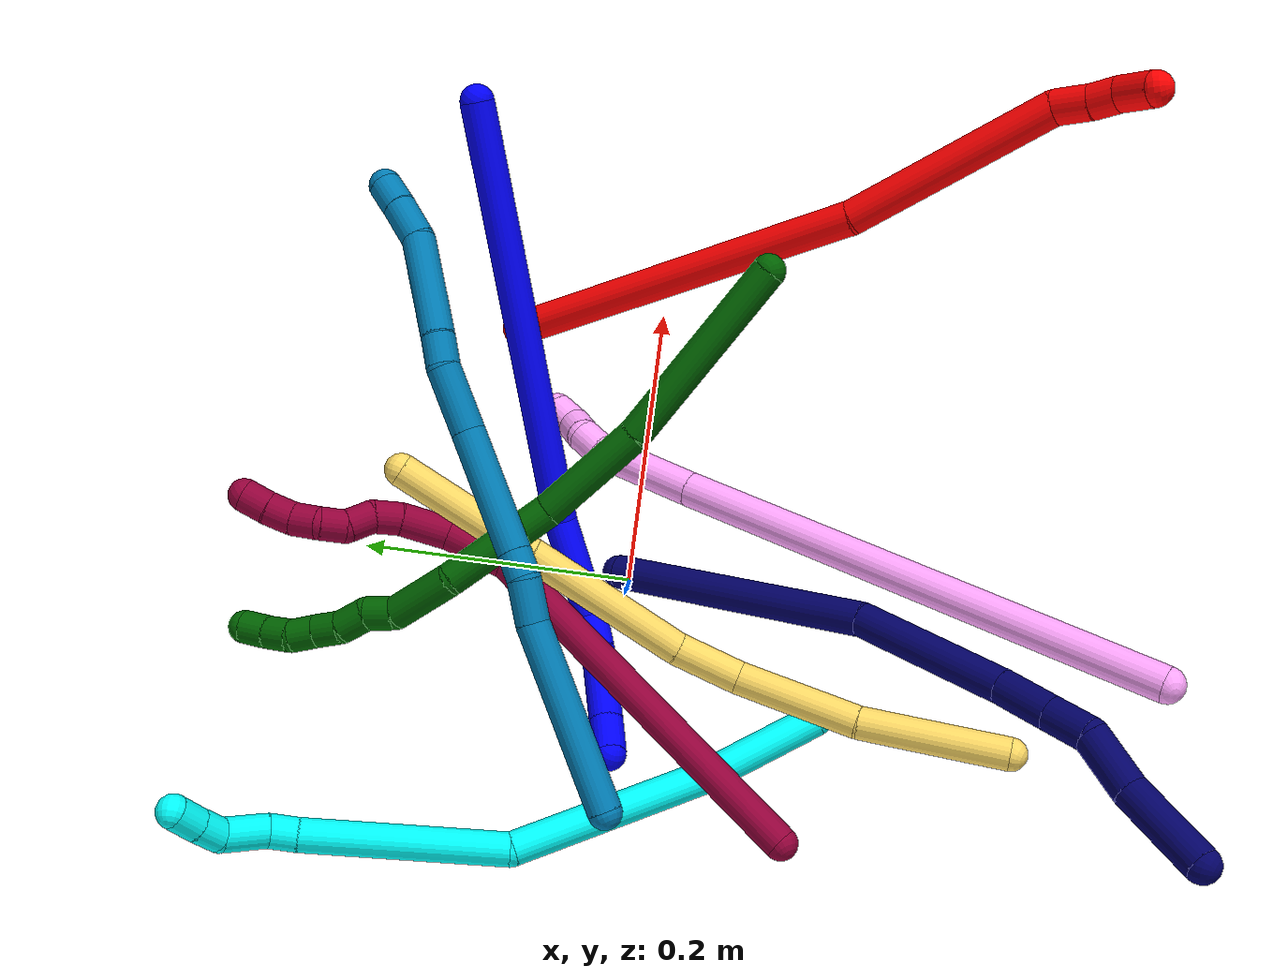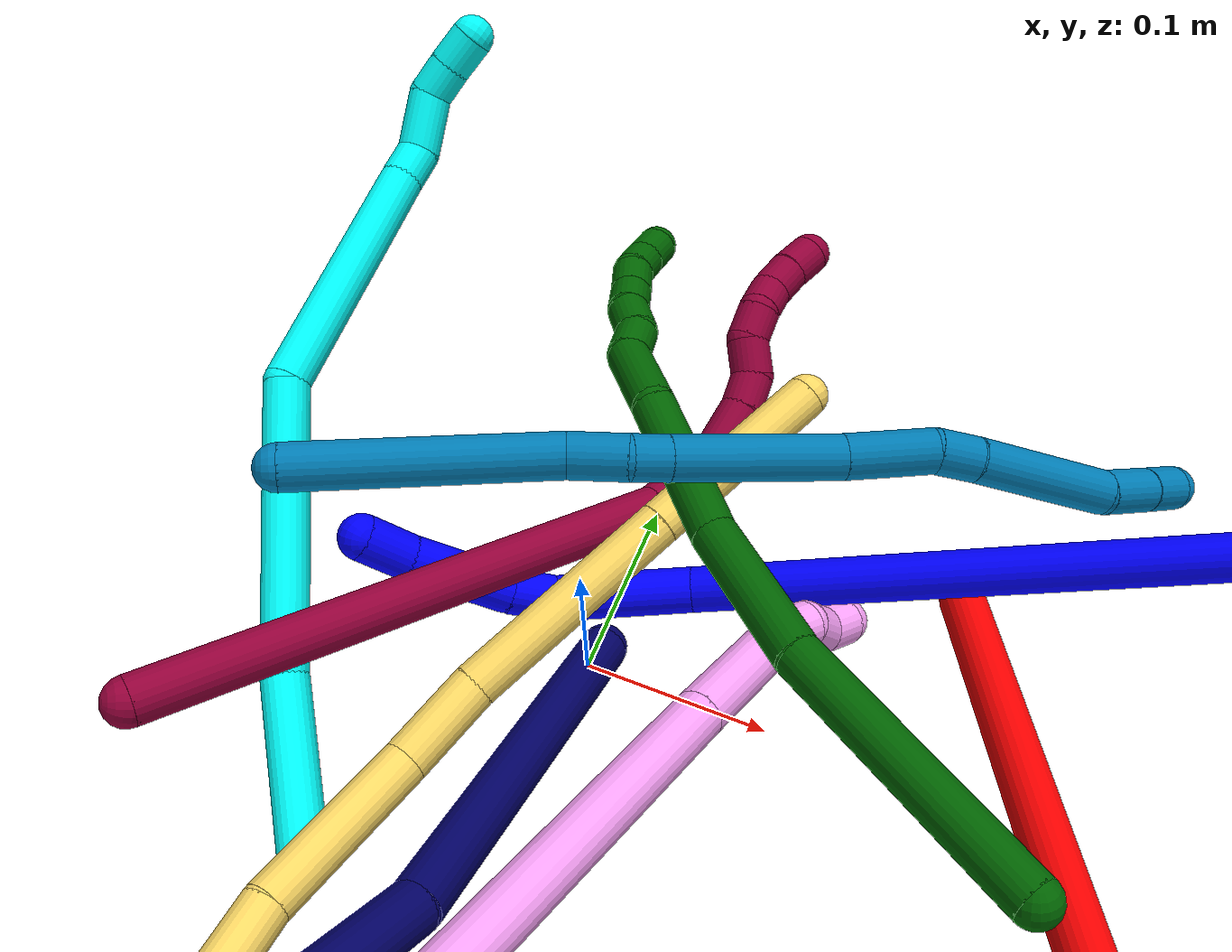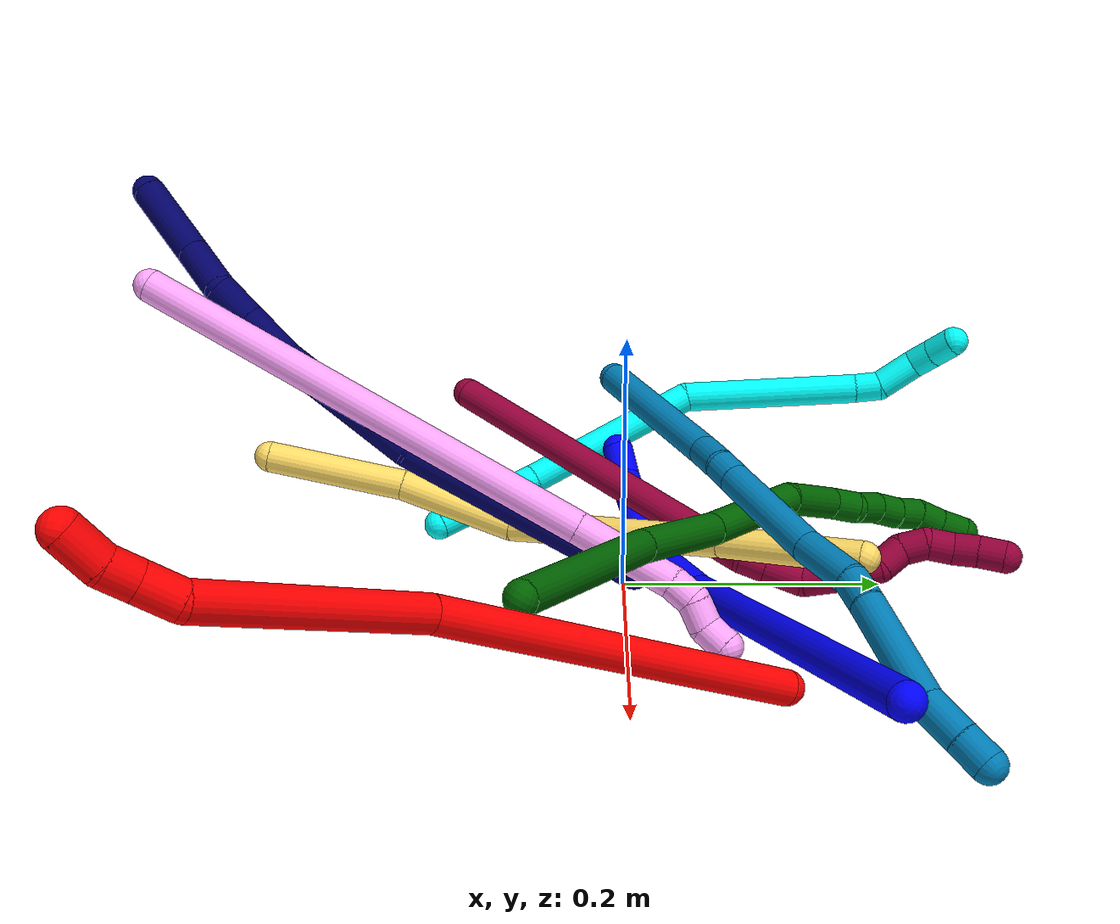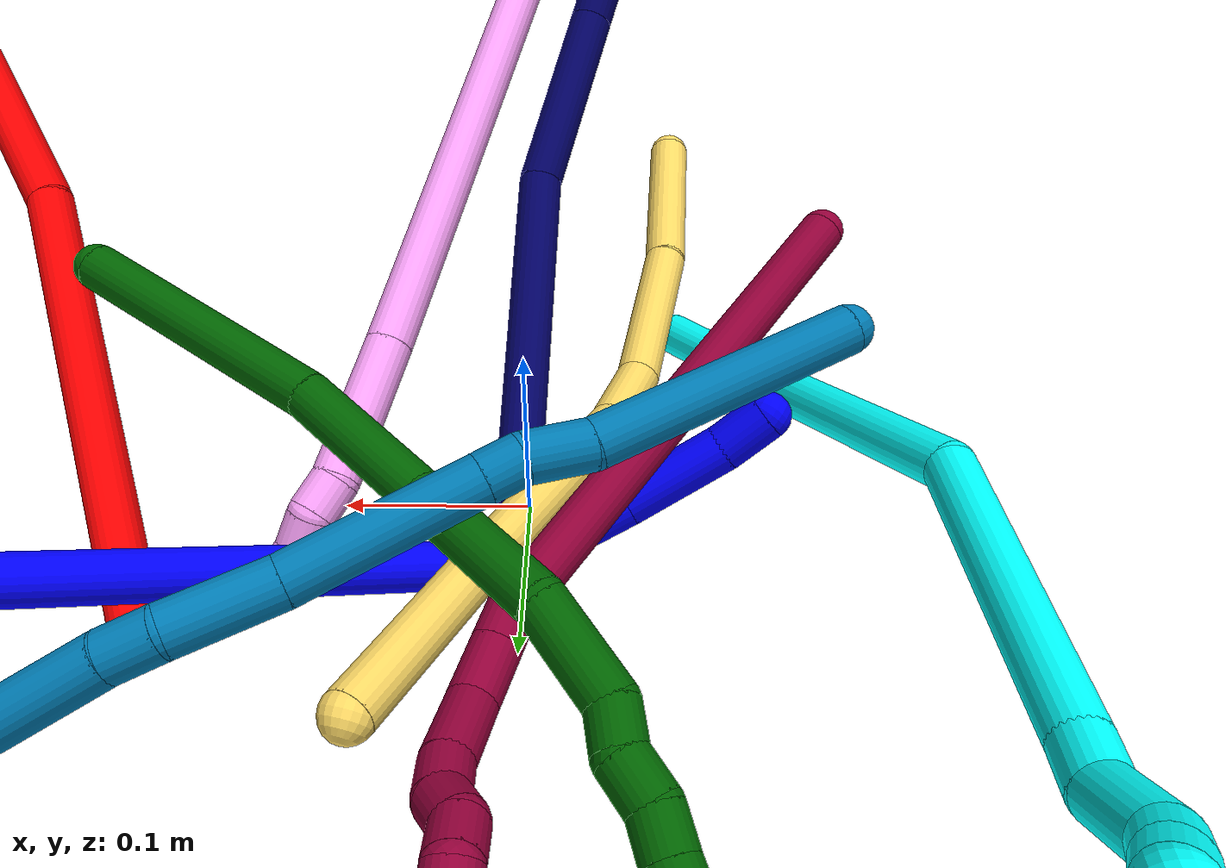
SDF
<sdf version="1.7">
 <world name="default">
  <plugin name="TubeGeneratorPlugin" filename="libtube_generator_plugin.so"/>
  <model name="photoneo_s_sensor">
   <static>1</static>
   <pose>0 0 2 1.57079 1.57079 3.14159</pose>
   <link name="link">
    <inertial><mass>0.1</mass></inertial>
    <sensor name="sensor" type="depth">
     <update_rate>30</update_rate>
     <camera>
      <horizontal_fov>1.22</horizontal_fov>
      <image><width>1920</width><height>1200</height><format>B8G8R8</format></image>
      <clip><near>0.1</near><far>4</far></clip>
      <depth_camera><output>points</output></depth_camera>
     </camera>
     <plugin name="camera_plugin" filename="libgazebo_ros_depth_camera.so">
      <baseline>0.2</baseline>
      <alwaysOn>1</alwaysOn>
      <updateRate>0.0</updateRate>
      <cameraName>camera_ir</cameraName>
      <imageTopicName>/camera/color/image_raw</imageTopicName>
      <cameraInfoTopicName>/camera/color/camera_info</cameraInfoTopicName>
      <depthImageTopicName>/camera/depth/image_raw</depthImageTopicName>
      <depthImageCameraInfoTopicName>/camera/depth/camera_info</depthImageCameraInfoTopicName>
      <pointCloudTopicName>/camera/depth/points</pointCloudTopicName>
      <frameName>fr_optical</frameName>
      <pointCloudCutoff>0.1</pointCloudCutoff>
      <pointCloudCutoffMax>2.0</pointCloudCutoffMax>
      <distortionK1>0</distortionK1>
      <distortionK2>0</distortionK2>
      <distortionK3>0</distortionK3>
      <distortionT1>0</distortionT1>
      <distortionT2>0</distortionT2>
      <CxPrime>0</CxPrime>
      <Cx>0</Cx>
      <Cy>0</Cy>
      <focalLength>0</focalLength>
      <hackBaseline>0</hackBaseline>
     </plugin>
    </sensor>
   </link>
  </model>
  <gravity>0 0 -9.8</gravity>
  <magnetic_field>6e-06 2.3e-05 -4.2e-05</magnetic_field>
  <atmosphere type="adiabatic"/>
  <physics name="default_physics" default="0" type="ode">
   <max_step_size>0.003</max_step_size>
   <real_time_factor>1</real_time_factor>
   <real_time_update_rate>1000</real_time_update_rate>
   <max_contacts>10000</max_contacts>
   <ode>
    <solver>
     <type>quick</type>
     <iters>100</iters>
     <sor>1.3</sor>
     <use_dynamic_moi_rescaling>0</use_dynamic_moi_rescaling>
    </solver>
    <constraints>
     <contact_max_correcting_vel>0</contact_max_correcting_vel>
     <contact_surface_layer>0.001</contact_surface_layer>
     <cfm>0</cfm>
     <erp>0.2</erp>
    </constraints>
   </ode>
  </physics>
  <scene><ambient>0.4 0.4 0.4 1</ambient><background>0.7 0.7 0.7 1</background><shadows>0</shadows></scene>
  <audio><device>default</device></audio>
  <spherical_coordinates>
   <surface_model>EARTH_WGS84</surface_model>
   <latitude_deg>0</latitude_deg>
   <longitude_deg>0</longitude_deg>
   <elevation>0</elevation>
   <heading_deg>0</heading_deg>
  </spherical_coordinates>
  <model name="bin">
   <static>1</static>
   <link name="bottom">
    <collision name="collision-bottom">
     <pose>0 0 -0.01 0 -0 0</pose>
     <geometry><box><size>0.8 0.6 0.02</size></box></geometry>
     <surface>
      <friction><ode><mu>100</mu><mu2>100</mu2></ode></friction>
      <contact><collide_bitmask>65535</collide_bitmask></contact>
     </surface>
    </collision>
   </link>
   <link name="west_wall">
    <collision name="collision-west_wall">
     <pose>-0.41 0 0.1 0 -0 0</pose>
     <geometry><box><size>0.02 0.6 0.2</size></box></geometry>
     <surface>
      <friction><ode><mu>100</mu><mu2>100</mu2></ode></friction>
      <contact><collide_bitmask>65535</collide_bitmask></contact>
     </surface>
    </collision>
   </link>
   <link name="east_wall">
    <collision name="collision-east_wall">
     <pose>0.41 0 0.1 0 -0 0</pose>
     <geometry><box><size>0.02 0.6 0.2</size></box></geometry>
     <surface>
      <friction><ode><mu>100</mu><mu2>100</mu2></ode></friction>
      <contact><collide_bitmask>65535</collide_bitmask></contact>
     </surface>
    </collision>
   </link>
   <link name="south_wall">
    <collision name="collision-south_wall">
     <pose>0 -0.31 0.1 0 -0 0</pose>
     <geometry><box><size>0.8 0.02 0.2</size></box></geometry>
     <surface>
      <friction><ode><mu>100</mu><mu2>100</mu2></ode></friction>
      <contact><collide_bitmask>65535</collide_bitmask></contact>
     </surface>
    </collision>
   </link>
   <link name="north_wall">
    <collision name="collision-north_wall">
     <pose>0 0.31 0.1 0 -0 0</pose>
     <geometry><box><size>0.8 0.02 0.2</size></box></geometry>
     <surface>
      <friction><ode><mu>100</mu><mu2>100</mu2></ode></friction>
      <contact><collide_bitmask>65535</collide_bitmask></contact>
     </surface>
    </collision>
   </link>
  </model>
  <model name="1">
   <static>0</static>
   <link name="1">
    <collision name="collision-cylinder-e_1_1_4">
     <pose>-0.062739 -0.072856 -0.123894 2.61001 -0.411581 -1.30832</pose>
     <geometry><cylinder><radius>0.0125</radius><length>0.313649</length></cylinder></geometry>
     <surface>
      <friction><ode><mu>1.16</mu><mu2>1.16</mu2><slip1>0</slip1><slip2>0</slip2></ode></friction>
      <contact><ode><kp>1e+06</kp><kd>1</kd><max_vel>0</max_vel><min_depth>0.001</min_depth></ode></contact>
     </surface>
    </collision>
    <visual name="visual-cylinder-e_1_1_4">
     <pose>-0.062739 -0.072856 -0.123894 2.61001 -0.411581 -1.30832</pose>
     <geometry><cylinder><radius>0.0125</radius><length>0.313649</length></cylinder></geometry>
     <material><ambient>0 0 1 1</ambient></material>
    </visual>
    <collision name="collision-cylinder-e_2_4_5">
     <pose>-0.148079 -0.164196 -0.271433 2.47806 -0.645461 -1.54111</pose>
     <geometry><cylinder><radius>0.0125</radius><length>0.075139</length></cylinder></geometry>
     <surface>
      <friction><ode><mu>1.16</mu><mu2>1.16</mu2><slip1>0</slip1><slip2>0</slip2></ode></friction>
      <contact><ode><kp>1e+06</kp><kd>1</kd><max_vel>0</max_vel><min_depth>0.001</min_depth></ode></contact>
     </surface>
    </collision>
    <visual name="visual-cylinder-e_2_4_5">
     <pose>-0.148079 -0.164196 -0.271433 2.47806 -0.645461 -1.54111</pose>
     <geometry><cylinder><radius>0.0125</radius><length>0.075139</length></cylinder></geometry>
     <material><ambient>0 0 1 1</ambient></material>
    </visual>
    <collision name="collision-cylinder-e_3_5_6">
     <pose>-0.181345 -0.186105 -0.300855 2.60652 -1.00873 -2.21977</pose>
     <geometry><cylinder><radius>0.0125</radius><length>0.02521</length></cylinder></geometry>
     <surface>
      <friction><ode><mu>1.16</mu><mu2>1.16</mu2><slip1>0</slip1><slip2>0</slip2></ode></friction>
      <contact><ode><kp>1e+06</kp><kd>1</kd><max_vel>0</max_vel><min_depth>0.001</min_depth></ode></contact>
     </surface>
    </collision>
    <visual name="visual-cylinder-e_3_5_6">
     <pose>-0.181345 -0.186105 -0.300855 2.60652 -1.00873 -2.21977</pose>
     <geometry><cylinder><radius>0.0125</radius><length>0.02521</length></cylinder></geometry>
     <material><ambient>0 0 1 1</ambient></material>
    </visual>
    <collision name="collision-cylinder-e_4_6_7">
     <pose>-0.218235 -0.193168 -0.318133 2.83525 -1.13971 -2.66875</pose>
     <geometry><cylinder><radius>0.0125</radius><length>0.057729</length></cylinder></geometry>
     <surface>
      <friction><ode><mu>1.16</mu><mu2>1.16</mu2><slip1>0</slip1><slip2>0</slip2></ode></friction>
      <contact><ode><kp>1e+06</kp><kd>1</kd><max_vel>0</max_vel><min_depth>0.001</min_depth></ode></contact>
     </surface>
    </collision>
    <visual name="visual-cylinder-e_4_6_7">
     <pose>-0.218235 -0.193168 -0.318133 2.83525 -1.13971 -2.66875</pose>
     <geometry><cylinder><radius>0.0125</radius><length>0.057729</length></cylinder></geometry>
     <material><ambient>0 0 1 1</ambient></material>
    </visual>
    <collision name="collision-cylinder-e_5_7_2">
     <pose>-0.258059 -0.197295 -0.333457 3.01426 -1.29458 -2.97333</pose>
     <geometry><cylinder><radius>0.0125</radius><length>0.028273</length></cylinder></geometry>
     <surface>
      <friction><ode><mu>1.16</mu><mu2>1.16</mu2><slip1>0</slip1><slip2>0</slip2></ode></friction>
      <contact><ode><kp>1e+06</kp><kd>1</kd><max_vel>0</max_vel><min_depth>0.001</min_depth></ode></contact>
     </surface>
    </collision>
    <visual name="visual-cylinder-e_5_7_2">
     <pose>-0.258059 -0.197295 -0.333457 3.01426 -1.29458 -2.97333</pose>
     <geometry><cylinder><radius>0.0125</radius><length>0.028273</length></cylinder></geometry>
     <material><ambient>0 0 1 1</ambient></material>
    </visual>
    <collision name="collision-sphere-2">
     <pose>-0.271659 -0.197784 -0.337281 0 -0 0</pose>
     <geometry><sphere><radius>0.0125</radius></sphere></geometry>
     <surface>
      <friction><ode><mu>1.16</mu><mu2>1.16</mu2><slip1>0</slip1><slip2>0</slip2></ode></friction>
      <contact><ode><kp>1e+06</kp><kd>1</kd><max_vel>0</max_vel><min_depth>0.001</min_depth></ode></contact>
     </surface>
    </collision>
    <visual name="visual-sphere-2">
     <pose>-0.271659 -0.197784 -0.337281 0 -0 0</pose>
     <geometry><sphere><radius>0.0125</radius></sphere></geometry>
     <material><ambient>0 0 1 1</ambient></material>
    </visual>
    <collision name="collision-sphere-7">
     <pose>-0.244458 -0.196805 -0.329633 0 -0 0</pose>
     <geometry><sphere><radius>0.0125</radius></sphere></geometry>
     <surface>
      <friction><ode><mu>1.16</mu><mu2>1.16</mu2><slip1>0</slip1><slip2>0</slip2></ode></friction>
      <contact><ode><kp>1e+06</kp><kd>1</kd><max_vel>0</max_vel><min_depth>0.001</min_depth></ode></contact>
     </surface>
    </collision>
    <visual name="visual-sphere-7">
     <pose>-0.244458 -0.196805 -0.329633 0 -0 0</pose>
     <geometry><sphere><radius>0.0125</radius></sphere></geometry>
     <material><ambient>0 0 1 1</ambient></material>
    </visual>
    <collision name="collision-sphere-6">
     <pose>-0.192011 -0.189531 -0.306633 0 -0 0</pose>
     <geometry><sphere><radius>0.0125</radius></sphere></geometry>
     <surface>
      <friction><ode><mu>1.16</mu><mu2>1.16</mu2><slip1>0</slip1><slip2>0</slip2></ode></friction>
      <contact><ode><kp>1e+06</kp><kd>1</kd><max_vel>0</max_vel><min_depth>0.001</min_depth></ode></contact>
     </surface>
    </collision>
    <visual name="visual-sphere-6">
     <pose>-0.192011 -0.189531 -0.306633 0 -0 0</pose>
     <geometry><sphere><radius>0.0125</radius></sphere></geometry>
     <material><ambient>0 0 1 1</ambient></material>
    </visual>
    <collision name="collision-sphere-5">
     <pose>-0.17068 -0.18268 -0.295076 0 -0 0</pose>
     <geometry><sphere><radius>0.0125</radius></sphere></geometry>
     <surface>
      <friction><ode><mu>1.16</mu><mu2>1.16</mu2><slip1>0</slip1><slip2>0</slip2></ode></friction>
      <contact><ode><kp>1e+06</kp><kd>1</kd><max_vel>0</max_vel><min_depth>0.001</min_depth></ode></contact>
     </surface>
    </collision>
    <visual name="visual-sphere-5">
     <pose>-0.17068 -0.18268 -0.295076 0 -0 0</pose>
     <geometry><sphere><radius>0.0125</radius></sphere></geometry>
     <material><ambient>0 0 1 1</ambient></material>
    </visual>
    <collision name="collision-sphere-1">
     <geometry><sphere><radius>0.0125</radius></sphere></geometry>
     <surface>
      <friction><ode><mu>1.16</mu><mu2>1.16</mu2><slip1>0</slip1><slip2>0</slip2></ode></friction>
      <contact><ode><kp>1e+06</kp><kd>1</kd><max_vel>0</max_vel><min_depth>0.001</min_depth></ode></contact>
     </surface>
    </collision>
    <visual name="visual-sphere-1">
     <geometry><sphere><radius>0.0125</radius></sphere></geometry>
     <material><ambient>0 0 1 1</ambient></material>
    </visual>
    <collision name="collision-sphere-4">
     <pose>-0.125478 -0.145712 -0.247789 0 -0 0</pose>
     <geometry><sphere><radius>0.0125</radius></sphere></geometry>
     <surface>
      <friction><ode><mu>1.16</mu><mu2>1.16</mu2><slip1>0</slip1><slip2>0</slip2></ode></friction>
      <contact><ode><kp>1e+06</kp><kd>1</kd><max_vel>0</max_vel><min_depth>0.001</min_depth></ode></contact>
     </surface>
    </collision>
    <visual name="visual-sphere-4">
     <pose>-0.125478 -0.145712 -0.247789 0 -0 0</pose>
     <geometry><sphere><radius>0.0125</radius></sphere></geometry>
     <material><ambient>0 0 1 1</ambient></material>
    </visual>
    <inertial>
     <pose>-0.110541 -0.11322 -0.189265 0 -0 0</pose>
     <mass>0.5</mass>
     <inertia>
      <ixx>-0.001736</ixx>
      <ixy>0</ixy>
      <ixz>0</ixz>
      <iyy>-0.002373</iyy>
      <iyz>0</iyz>
      <izz>0.002274</izz>
     </inertia>
    </inertial>
   </link>
   <pose>0.326875 0.150113 0.092258 0.653339 0.900551 0.427882</pose>
  </model>
  <model name="2">
   <static>0</static>
   <link name="2">
    <collision name="collision-cylinder-e_1_1_4">
     <pose>0.014593 -0.017977 0.133135 0.134215 0.108197 0.007279</pose>
     <geometry><cylinder><radius>0.0125</radius><length>0.270268</length></cylinder></geometry>
     <surface>
      <friction><ode><mu>1.16</mu><mu2>1.16</mu2><slip1>0</slip1><slip2>0</slip2></ode></friction>
      <contact><ode><kp>1e+06</kp><kd>1</kd><max_vel>0</max_vel><min_depth>0.001</min_depth></ode></contact>
     </surface>
    </collision>
    <visual name="visual-cylinder-e_1_1_4">
     <pose>0.014593 -0.017977 0.133135 0.134215 0.108197 0.007279</pose>
     <geometry><cylinder><radius>0.0125</radius><length>0.270268</length></cylinder></geometry>
     <material><ambient>1 0 0 1</ambient></material>
    </visual>
    <collision name="collision-cylinder-e_2_4_5">
     <pose>0.036583 -0.060967 0.339736 0.328163 0.095043 0.015748</pose>
     <geometry><cylinder><radius>0.0125</radius><length>0.155917</length></cylinder></geometry>
     <surface>
      <friction><ode><mu>1.16</mu><mu2>1.16</mu2><slip1>0</slip1><slip2>0</slip2></ode></friction>
      <contact><ode><kp>1e+06</kp><kd>1</kd><max_vel>0</max_vel><min_depth>0.001</min_depth></ode></contact>
     </surface>
    </collision>
    <visual name="visual-cylinder-e_2_4_5">
     <pose>0.036583 -0.060967 0.339736 0.328163 0.095043 0.015748</pose>
     <geometry><cylinder><radius>0.0125</radius><length>0.155917</length></cylinder></geometry>
     <material><ambient>1 0 0 1</ambient></material>
    </visual>
    <collision name="collision-cylinder-e_3_5_6">
     <pose>0.046547 -0.084586 0.426036 -0.108176 0.196162 -0.010654</pose>
     <geometry><cylinder><radius>0.0125</radius><length>0.026325</length></cylinder></geometry>
     <surface>
      <friction><ode><mu>1.16</mu><mu2>1.16</mu2><slip1>0</slip1><slip2>0</slip2></ode></friction>
      <contact><ode><kp>1e+06</kp><kd>1</kd><max_vel>0</max_vel><min_depth>0.001</min_depth></ode></contact>
     </surface>
    </collision>
    <visual name="visual-cylinder-e_3_5_6">
     <pose>0.046547 -0.084586 0.426036 -0.108176 0.196162 -0.010654</pose>
     <geometry><cylinder><radius>0.0125</radius><length>0.026325</length></cylinder></geometry>
     <material><ambient>1 0 0 1</ambient></material>
    </visual>
    <collision name="collision-cylinder-e_4_6_7">
     <pose>0.05184 -0.083127 0.448569 -0.00671 0.274141 -0.000926</pose>
     <geometry><cylinder><radius>0.0125</radius><length>0.020149</length></cylinder></geometry>
     <surface>
      <friction><ode><mu>1.16</mu><mu2>1.16</mu2><slip1>0</slip1><slip2>0</slip2></ode></friction>
      <contact><ode><kp>1e+06</kp><kd>1</kd><max_vel>0</max_vel><min_depth>0.001</min_depth></ode></contact>
     </surface>
    </collision>
    <visual name="visual-cylinder-e_4_6_7">
     <pose>0.05184 -0.083127 0.448569 -0.00671 0.274141 -0.000926</pose>
     <geometry><cylinder><radius>0.0125</radius><length>0.020149</length></cylinder></geometry>
     <material><ambient>1 0 0 1</ambient></material>
    </visual>
    <collision name="collision-cylinder-e_5_7_2">
     <pose>0.060793 -0.080132 0.470079 -0.243174 0.472851 -0.058862</pose>
     <geometry><cylinder><radius>0.0125</radius><length>0.027341</length></cylinder></geometry>
     <surface>
      <friction><ode><mu>1.16</mu><mu2>1.16</mu2><slip1>0</slip1><slip2>0</slip2></ode></friction>
      <contact><ode><kp>1e+06</kp><kd>1</kd><max_vel>0</max_vel><min_depth>0.001</min_depth></ode></contact>
     </surface>
    </collision>
    <visual name="visual-cylinder-e_5_7_2">
     <pose>0.060793 -0.080132 0.470079 -0.243174 0.472851 -0.058862</pose>
     <geometry><cylinder><radius>0.0125</radius><length>0.027341</length></cylinder></geometry>
     <material><ambient>1 0 0 1</ambient></material>
    </visual>
    <collision name="collision-sphere-2">
     <pose>0.067019 -0.077201 0.481892 0 -0 0</pose>
     <geometry><sphere><radius>0.0125</radius></sphere></geometry>
     <surface>
      <friction><ode><mu>1.16</mu><mu2>1.16</mu2><slip1>0</slip1><slip2>0</slip2></ode></friction>
      <contact><ode><kp>1e+06</kp><kd>1</kd><max_vel>0</max_vel><min_depth>0.001</min_depth></ode></contact>
     </surface>
    </collision>
    <visual name="visual-sphere-2">
     <pose>0.067019 -0.077201 0.481892 0 -0 0</pose>
     <geometry><sphere><radius>0.0125</radius></sphere></geometry>
     <material><ambient>1 0 0 1</ambient></material>
    </visual>
    <collision name="collision-sphere-7">
     <pose>0.054567 -0.083062 0.458267 0 -0 0</pose>
     <geometry><sphere><radius>0.0125</radius></sphere></geometry>
     <surface>
      <friction><ode><mu>1.16</mu><mu2>1.16</mu2><slip1>0</slip1><slip2>0</slip2></ode></friction>
      <contact><ode><kp>1e+06</kp><kd>1</kd><max_vel>0</max_vel><min_depth>0.001</min_depth></ode></contact>
     </surface>
    </collision>
    <visual name="visual-sphere-7">
     <pose>0.054567 -0.083062 0.458267 0 -0 0</pose>
     <geometry><sphere><radius>0.0125</radius></sphere></geometry>
     <material><ambient>1 0 0 1</ambient></material>
    </visual>
    <collision name="collision-sphere-6">
     <pose>0.049113 -0.083192 0.438871 0 -0 0</pose>
     <geometry><sphere><radius>0.0125</radius></sphere></geometry>
     <surface>
      <friction><ode><mu>1.16</mu><mu2>1.16</mu2><slip1>0</slip1><slip2>0</slip2></ode></friction>
      <contact><ode><kp>1e+06</kp><kd>1</kd><max_vel>0</max_vel><min_depth>0.001</min_depth></ode></contact>
     </surface>
    </collision>
    <visual name="visual-sphere-6">
     <pose>0.049113 -0.083192 0.438871 0 -0 0</pose>
     <geometry><sphere><radius>0.0125</radius></sphere></geometry>
     <material><ambient>1 0 0 1</ambient></material>
    </visual>
    <collision name="collision-sphere-5">
     <pose>0.043982 -0.08598 0.413201 0 -0 0</pose>
     <geometry><sphere><radius>0.0125</radius></sphere></geometry>
     <surface>
      <friction><ode><mu>1.16</mu><mu2>1.16</mu2><slip1>0</slip1><slip2>0</slip2></ode></friction>
      <contact><ode><kp>1e+06</kp><kd>1</kd><max_vel>0</max_vel><min_depth>0.001</min_depth></ode></contact>
     </surface>
    </collision>
    <visual name="visual-sphere-5">
     <pose>0.043982 -0.08598 0.413201 0 -0 0</pose>
     <geometry><sphere><radius>0.0125</radius></sphere></geometry>
     <material><ambient>1 0 0 1</ambient></material>
    </visual>
    <collision name="collision-sphere-1">
     <geometry><sphere><radius>0.0125</radius></sphere></geometry>
     <surface>
      <friction><ode><mu>1.16</mu><mu2>1.16</mu2><slip1>0</slip1><slip2>0</slip2></ode></friction>
      <contact><ode><kp>1e+06</kp><kd>1</kd><max_vel>0</max_vel><min_depth>0.001</min_depth></ode></contact>
     </surface>
    </collision>
    <visual name="visual-sphere-1">
     <geometry><sphere><radius>0.0125</radius></sphere></geometry>
     <material><ambient>1 0 0 1</ambient></material>
    </visual>
    <collision name="collision-sphere-4">
     <pose>0.029185 -0.035954 0.266271 0 -0 0</pose>
     <geometry><sphere><radius>0.0125</radius></sphere></geometry>
     <surface>
      <friction><ode><mu>1.16</mu><mu2>1.16</mu2><slip1>0</slip1><slip2>0</slip2></ode></friction>
      <contact><ode><kp>1e+06</kp><kd>1</kd><max_vel>0</max_vel><min_depth>0.001</min_depth></ode></contact>
     </surface>
    </collision>
    <visual name="visual-sphere-4">
     <pose>0.029185 -0.035954 0.266271 0 -0 0</pose>
     <geometry><sphere><radius>0.0125</radius></sphere></geometry>
     <material><ambient>1 0 0 1</ambient></material>
    </visual>
    <inertial>
     <pose>0.02716 -0.040914 0.244118 0 -0 0</pose>
     <mass>0.5</mass>
     <inertia>
      <ixx>0.001995</ixx>
      <ixy>0</ixy>
      <ixz>0</ixz>
      <iyy>0.001963</iyy>
      <iyz>0</iyz>
      <izz>0.000149</izz>
     </inertia>
    </inertial>
   </link>
   <pose>0.17664 0.105623 0.011497 0.609966 -1.14692 1.15647</pose>
  </model>
  <model name="3">
   <static>0</static>
   <link name="3">
    <collision name="collision-cylinder-e_1_1_4">
     <pose>-0.010146 0.037655 0.026196 -0.96298 -0.217681 0.114067</pose>
     <geometry><cylinder><radius>0.0125</radius><length>0.093959</length></cylinder></geometry>
     <surface>
      <friction><ode><mu>1.16</mu><mu2>1.16</mu2><slip1>0</slip1><slip2>0</slip2></ode></friction>
      <contact><ode><kp>1e+06</kp><kd>1</kd><max_vel>0</max_vel><min_depth>0.001</min_depth></ode></contact>
     </surface>
    </collision>
    <visual name="visual-cylinder-e_1_1_4">
     <pose>-0.010146 0.037655 0.026196 -0.96298 -0.217681 0.114067</pose>
     <geometry><cylinder><radius>0.0125</radius><length>0.093959</length></cylinder></geometry>
     <material><ambient>0.003922 1 0.996078 1</ambient></material>
    </visual>
    <collision name="collision-cylinder-e_2_4_5">
     <pose>-0.023639 0.142238 0.09208 -1.03553 -0.042992 0.024491</pose>
     <geometry><cylinder><radius>0.0125</radius><length>0.155765</length></cylinder></geometry>
     <surface>
      <friction><ode><mu>1.16</mu><mu2>1.16</mu2><slip1>0</slip1><slip2>0</slip2></ode></friction>
      <contact><ode><kp>1e+06</kp><kd>1</kd><max_vel>0</max_vel><min_depth>0.001</min_depth></ode></contact>
     </surface>
    </collision>
    <visual name="visual-cylinder-e_2_4_5">
     <pose>-0.023639 0.142238 0.09208 -1.03553 -0.042992 0.024491</pose>
     <geometry><cylinder><radius>0.0125</radius><length>0.155765</length></cylinder></geometry>
     <material><ambient>0.003922 1 0.996078 1</ambient></material>
    </visual>
    <collision name="collision-cylinder-e_3_5_6">
     <pose>-0.037192 0.283541 0.136069 -1.51305 -0.13614 0.128518</pose>
     <geometry><cylinder><radius>0.0125</radius><length>0.15039</length></cylinder></geometry>
     <surface>
      <friction><ode><mu>1.16</mu><mu2>1.16</mu2><slip1>0</slip1><slip2>0</slip2></ode></friction>
      <contact><ode><kp>1e+06</kp><kd>1</kd><max_vel>0</max_vel><min_depth>0.001</min_depth></ode></contact>
     </surface>
    </collision>
    <visual name="visual-cylinder-e_3_5_6">
     <pose>-0.037192 0.283541 0.136069 -1.51305 -0.13614 0.128518</pose>
     <geometry><cylinder><radius>0.0125</radius><length>0.15039</length></cylinder></geometry>
     <material><ambient>0.003922 1 0.996078 1</ambient></material>
    </visual>
    <collision name="collision-cylinder-e_4_6_7">
     <pose>-0.047616 0.368954 0.140711 -1.53979 -0.019822 0.019216</pose>
     <geometry><cylinder><radius>0.0125</radius><length>0.022091</length></cylinder></geometry>
     <surface>
      <friction><ode><mu>1.16</mu><mu2>1.16</mu2><slip1>0</slip1><slip2>0</slip2></ode></friction>
      <contact><ode><kp>1e+06</kp><kd>1</kd><max_vel>0</max_vel><min_depth>0.001</min_depth></ode></contact>
     </surface>
    </collision>
    <visual name="visual-cylinder-e_4_6_7">
     <pose>-0.047616 0.368954 0.140711 -1.53979 -0.019822 0.019216</pose>
     <geometry><cylinder><radius>0.0125</radius><length>0.022091</length></cylinder></geometry>
     <material><ambient>0.003922 1 0.996078 1</ambient></material>
    </visual>
    <collision name="collision-cylinder-e_5_7_8">
     <pose>-0.042788 0.39557 0.147609 -1.17247 0.290194 -0.193481</pose>
     <geometry><cylinder><radius>0.0125</radius><length>0.035278</length></cylinder></geometry>
     <surface>
      <friction><ode><mu>1.16</mu><mu2>1.16</mu2><slip1>0</slip1><slip2>0</slip2></ode></friction>
      <contact><ode><kp>1e+06</kp><kd>1</kd><max_vel>0</max_vel><min_depth>0.001</min_depth></ode></contact>
     </surface>
    </collision>
    <visual name="visual-cylinder-e_5_7_8">
     <pose>-0.042788 0.39557 0.147609 -1.17247 0.290194 -0.193481</pose>
     <geometry><cylinder><radius>0.0125</radius><length>0.035278</length></cylinder></geometry>
     <material><ambient>0.003922 1 0.996078 1</ambient></material>
    </visual>
    <collision name="collision-cylinder-e_6_8_9">
     <pose>-0.031411 0.419367 0.154157 -1.57173 0.656287 -0.656855</pose>
     <geometry><cylinder><radius>0.0125</radius><length>0.020748</length></cylinder></geometry>
     <surface>
      <friction><ode><mu>1.16</mu><mu2>1.16</mu2><slip1>0</slip1><slip2>0</slip2></ode></friction>
      <contact><ode><kp>1e+06</kp><kd>1</kd><max_vel>0</max_vel><min_depth>0.001</min_depth></ode></contact>
     </surface>
    </collision>
    <visual name="visual-cylinder-e_6_8_9">
     <pose>-0.031411 0.419367 0.154157 -1.57173 0.656287 -0.656855</pose>
     <geometry><cylinder><radius>0.0125</radius><length>0.020748</length></cylinder></geometry>
     <material><ambient>0.003922 1 0.996078 1</ambient></material>
    </visual>
    <collision name="collision-cylinder-e_7_9_2">
     <pose>-0.01798 0.435822 0.153676 -1.62825 0.71075 -0.749075</pose>
     <geometry><cylinder><radius>0.0125</radius><length>0.021769</length></cylinder></geometry>
     <surface>
      <friction><ode><mu>1.16</mu><mu2>1.16</mu2><slip1>0</slip1><slip2>0</slip2></ode></friction>
      <contact><ode><kp>1e+06</kp><kd>1</kd><max_vel>0</max_vel><min_depth>0.001</min_depth></ode></contact>
     </surface>
    </collision>
    <visual name="visual-cylinder-e_7_9_2">
     <pose>-0.01798 0.435822 0.153676 -1.62825 0.71075 -0.749075</pose>
     <geometry><cylinder><radius>0.0125</radius><length>0.021769</length></cylinder></geometry>
     <material><ambient>0.003922 1 0.996078 1</ambient></material>
    </visual>
    <collision name="collision-sphere-2">
     <pose>-0.010879 0.444057 0.153202 0 -0 0</pose>
     <geometry><sphere><radius>0.0125</radius></sphere></geometry>
     <surface>
      <friction><ode><mu>1.16</mu><mu2>1.16</mu2><slip1>0</slip1><slip2>0</slip2></ode></friction>
      <contact><ode><kp>1e+06</kp><kd>1</kd><max_vel>0</max_vel><min_depth>0.001</min_depth></ode></contact>
     </surface>
    </collision>
    <visual name="visual-sphere-2">
     <pose>-0.010879 0.444057 0.153202 0 -0 0</pose>
     <geometry><sphere><radius>0.0125</radius></sphere></geometry>
     <material><ambient>0.003922 1 0.996078 1</ambient></material>
    </visual>
    <collision name="collision-sphere-9">
     <pose>-0.025081 0.427586 0.154149 0 -0 0</pose>
     <geometry><sphere><radius>0.0125</radius></sphere></geometry>
     <surface>
      <friction><ode><mu>1.16</mu><mu2>1.16</mu2><slip1>0</slip1><slip2>0</slip2></ode></friction>
      <contact><ode><kp>1e+06</kp><kd>1</kd><max_vel>0</max_vel><min_depth>0.001</min_depth></ode></contact>
     </surface>
    </collision>
    <visual name="visual-sphere-9">
     <pose>-0.025081 0.427586 0.154149 0 -0 0</pose>
     <geometry><sphere><radius>0.0125</radius></sphere></geometry>
     <material><ambient>0.003922 1 0.996078 1</ambient></material>
    </visual>
    <collision name="collision-sphere-4">
     <pose>-0.020292 0.075311 0.052392 0 -0 0</pose>
     <geometry><sphere><radius>0.0125</radius></sphere></geometry>
     <surface>
      <friction><ode><mu>1.16</mu><mu2>1.16</mu2><slip1>0</slip1><slip2>0</slip2></ode></friction>
      <contact><ode><kp>1e+06</kp><kd>1</kd><max_vel>0</max_vel><min_depth>0.001</min_depth></ode></contact>
     </surface>
    </collision>
    <visual name="visual-sphere-4">
     <pose>-0.020292 0.075311 0.052392 0 -0 0</pose>
     <geometry><sphere><radius>0.0125</radius></sphere></geometry>
     <material><ambient>0.003922 1 0.996078 1</ambient></material>
    </visual>
    <collision name="collision-sphere-1">
     <geometry><sphere><radius>0.0125</radius></sphere></geometry>
     <surface>
      <friction><ode><mu>1.16</mu><mu2>1.16</mu2><slip1>0</slip1><slip2>0</slip2></ode></friction>
      <contact><ode><kp>1e+06</kp><kd>1</kd><max_vel>0</max_vel><min_depth>0.001</min_depth></ode></contact>
     </surface>
    </collision>
    <visual name="visual-sphere-1">
     <geometry><sphere><radius>0.0125</radius></sphere></geometry>
     <material><ambient>0.003922 1 0.996078 1</ambient></material>
    </visual>
    <collision name="collision-sphere-8">
     <pose>-0.037741 0.411148 0.154165 0 -0 0</pose>
     <geometry><sphere><radius>0.0125</radius></sphere></geometry>
     <surface>
      <friction><ode><mu>1.16</mu><mu2>1.16</mu2><slip1>0</slip1><slip2>0</slip2></ode></friction>
      <contact><ode><kp>1e+06</kp><kd>1</kd><max_vel>0</max_vel><min_depth>0.001</min_depth></ode></contact>
     </surface>
    </collision>
    <visual name="visual-sphere-8">
     <pose>-0.037741 0.411148 0.154165 0 -0 0</pose>
     <geometry><sphere><radius>0.0125</radius></sphere></geometry>
     <material><ambient>0.003922 1 0.996078 1</ambient></material>
    </visual>
    <collision name="collision-sphere-5">
     <pose>-0.026987 0.209166 0.131769 0 -0 0</pose>
     <geometry><sphere><radius>0.0125</radius></sphere></geometry>
     <surface>
      <friction><ode><mu>1.16</mu><mu2>1.16</mu2><slip1>0</slip1><slip2>0</slip2></ode></friction>
      <contact><ode><kp>1e+06</kp><kd>1</kd><max_vel>0</max_vel><min_depth>0.001</min_depth></ode></contact>
     </surface>
    </collision>
    <visual name="visual-sphere-5">
     <pose>-0.026987 0.209166 0.131769 0 -0 0</pose>
     <geometry><sphere><radius>0.0125</radius></sphere></geometry>
     <material><ambient>0.003922 1 0.996078 1</ambient></material>
    </visual>
    <collision name="collision-sphere-6">
     <pose>-0.047397 0.357916 0.140369 0 -0 0</pose>
     <geometry><sphere><radius>0.0125</radius></sphere></geometry>
     <surface>
      <friction><ode><mu>1.16</mu><mu2>1.16</mu2><slip1>0</slip1><slip2>0</slip2></ode></friction>
      <contact><ode><kp>1e+06</kp><kd>1</kd><max_vel>0</max_vel><min_depth>0.001</min_depth></ode></contact>
     </surface>
    </collision>
    <visual name="visual-sphere-6">
     <pose>-0.047397 0.357916 0.140369 0 -0 0</pose>
     <geometry><sphere><radius>0.0125</radius></sphere></geometry>
     <material><ambient>0.003922 1 0.996078 1</ambient></material>
    </visual>
    <collision name="collision-sphere-7">
     <pose>-0.047835 0.379992 0.141054 0 -0 0</pose>
     <geometry><sphere><radius>0.0125</radius></sphere></geometry>
     <surface>
      <friction><ode><mu>1.16</mu><mu2>1.16</mu2><slip1>0</slip1><slip2>0</slip2></ode></friction>
      <contact><ode><kp>1e+06</kp><kd>1</kd><max_vel>0</max_vel><min_depth>0.001</min_depth></ode></contact>
     </surface>
    </collision>
    <visual name="visual-sphere-7">
     <pose>-0.047835 0.379992 0.141054 0 -0 0</pose>
     <geometry><sphere><radius>0.0125</radius></sphere></geometry>
     <material><ambient>0.003922 1 0.996078 1</ambient></material>
    </visual>
    <inertial>
     <pose>-0.027667 0.217259 0.104254 0 -0 0</pose>
     <mass>0.5</mass>
     <inertia>
      <ixx>0.000733</ixx>
      <ixy>0</ixy>
      <ixz>0</ixz>
      <iyy>0.000317</iyy>
      <iyz>0</iyz>
      <izz>-0.000552</izz>
     </inertia>
    </inertial>
   </link>
   <pose>-0.085157 -0.151403 0.011499 0.229233 -0.99856 -0.260693</pose>
  </model>
  <model name="4">
   <static>0</static>
   <link name="4">
    <collision name="collision-cylinder-e_1_1_4">
     <pose>0.002408 0.125193 -0.129861 -2.37449 0.01335 -0.033079</pose>
     <geometry><cylinder><radius>0.0125</radius><length>0.360792</length></cylinder></geometry>
     <surface>
      <friction><ode><mu>1.16</mu><mu2>1.16</mu2><slip1>0</slip1><slip2>0</slip2></ode></friction>
      <contact><ode><kp>1e+06</kp><kd>1</kd><max_vel>0</max_vel><min_depth>0.001</min_depth></ode></contact>
     </surface>
    </collision>
    <visual name="visual-cylinder-e_1_1_4">
     <pose>0.002408 0.125193 -0.129861 -2.37449 0.01335 -0.033079</pose>
     <geometry><cylinder><radius>0.0125</radius><length>0.360792</length></cylinder></geometry>
     <material><ambient>1 0.65098 0.996078 1</ambient></material>
    </visual>
    <collision name="collision-cylinder-e_2_4_5">
     <pose>0.005937 0.277446 -0.288179 -2.38136 0.028537 -0.071397</pose>
     <geometry><cylinder><radius>0.0125</radius><length>0.078572</length></cylinder></geometry>
     <surface>
      <friction><ode><mu>1.16</mu><mu2>1.16</mu2><slip1>0</slip1><slip2>0</slip2></ode></friction>
      <contact><ode><kp>1e+06</kp><kd>1</kd><max_vel>0</max_vel><min_depth>0.001</min_depth></ode></contact>
     </surface>
    </collision>
    <visual name="visual-cylinder-e_2_4_5">
     <pose>0.005937 0.277446 -0.288179 -2.38136 0.028537 -0.071397</pose>
     <geometry><cylinder><radius>0.0125</radius><length>0.078572</length></cylinder></geometry>
     <material><ambient>1 0.65098 0.996078 1</ambient></material>
    </visual>
    <collision name="collision-cylinder-e_3_5_6">
     <pose>0.009471 0.309793 -0.324791 -2.56636 0.243418 -0.784136</pose>
     <geometry><cylinder><radius>0.0125</radius><length>0.020025</length></cylinder></geometry>
     <surface>
      <friction><ode><mu>1.16</mu><mu2>1.16</mu2><slip1>0</slip1><slip2>0</slip2></ode></friction>
      <contact><ode><kp>1e+06</kp><kd>1</kd><max_vel>0</max_vel><min_depth>0.001</min_depth></ode></contact>
     </surface>
    </collision>
    <visual name="visual-cylinder-e_3_5_6">
     <pose>0.009471 0.309793 -0.324791 -2.56636 0.243418 -0.784136</pose>
     <geometry><cylinder><radius>0.0125</radius><length>0.020025</length></cylinder></geometry>
     <material><ambient>1 0.65098 0.996078 1</ambient></material>
    </visual>
    <collision name="collision-cylinder-e_4_6_7">
     <pose>0.011745 0.316365 -0.343088 -3.0155 -0.013694 0.216081</pose>
     <geometry><cylinder><radius>0.0125</radius><length>0.020452</length></cylinder></geometry>
     <surface>
      <friction><ode><mu>1.16</mu><mu2>1.16</mu2><slip1>0</slip1><slip2>0</slip2></ode></friction>
      <contact><ode><kp>1e+06</kp><kd>1</kd><max_vel>0</max_vel><min_depth>0.001</min_depth></ode></contact>
     </surface>
    </collision>
    <visual name="visual-cylinder-e_4_6_7">
     <pose>0.011745 0.316365 -0.343088 -3.0155 -0.013694 0.216081</pose>
     <geometry><cylinder><radius>0.0125</radius><length>0.020452</length></cylinder></geometry>
     <material><ambient>1 0.65098 0.996078 1</ambient></material>
    </visual>
    <collision name="collision-cylinder-e_5_7_2">
     <pose>0.013702 0.322766 -0.361659 -2.59609 0.209675 -0.719592</pose>
     <geometry><cylinder><radius>0.0125</radius><length>0.020159</length></cylinder></geometry>
     <surface>
      <friction><ode><mu>1.16</mu><mu2>1.16</mu2><slip1>0</slip1><slip2>0</slip2></ode></friction>
      <contact><ode><kp>1e+06</kp><kd>1</kd><max_vel>0</max_vel><min_depth>0.001</min_depth></ode></contact>
     </surface>
    </collision>
    <visual name="visual-cylinder-e_5_7_2">
     <pose>0.013702 0.322766 -0.361659 -2.59609 0.209675 -0.719592</pose>
     <geometry><cylinder><radius>0.0125</radius><length>0.020159</length></cylinder></geometry>
     <material><ambient>1 0.65098 0.996078 1</ambient></material>
    </visual>
    <collision name="collision-sphere-2">
     <pose>0.0158 0.327882 -0.370087 0 -0 0</pose>
     <geometry><sphere><radius>0.0125</radius></sphere></geometry>
     <surface>
      <friction><ode><mu>1.16</mu><mu2>1.16</mu2><slip1>0</slip1><slip2>0</slip2></ode></friction>
      <contact><ode><kp>1e+06</kp><kd>1</kd><max_vel>0</max_vel><min_depth>0.001</min_depth></ode></contact>
     </surface>
    </collision>
    <visual name="visual-sphere-2">
     <pose>0.0158 0.327882 -0.370087 0 -0 0</pose>
     <geometry><sphere><radius>0.0125</radius></sphere></geometry>
     <material><ambient>1 0.65098 0.996078 1</ambient></material>
    </visual>
    <collision name="collision-sphere-7">
     <pose>0.011605 0.317651 -0.353231 0 -0 0</pose>
     <geometry><sphere><radius>0.0125</radius></sphere></geometry>
     <surface>
      <friction><ode><mu>1.16</mu><mu2>1.16</mu2><slip1>0</slip1><slip2>0</slip2></ode></friction>
      <contact><ode><kp>1e+06</kp><kd>1</kd><max_vel>0</max_vel><min_depth>0.001</min_depth></ode></contact>
     </surface>
    </collision>
    <visual name="visual-sphere-7">
     <pose>0.011605 0.317651 -0.353231 0 -0 0</pose>
     <geometry><sphere><radius>0.0125</radius></sphere></geometry>
     <material><ambient>1 0.65098 0.996078 1</ambient></material>
    </visual>
    <collision name="collision-sphere-6">
     <pose>0.011885 0.315079 -0.332944 0 -0 0</pose>
     <geometry><sphere><radius>0.0125</radius></sphere></geometry>
     <surface>
      <friction><ode><mu>1.16</mu><mu2>1.16</mu2><slip1>0</slip1><slip2>0</slip2></ode></friction>
      <contact><ode><kp>1e+06</kp><kd>1</kd><max_vel>0</max_vel><min_depth>0.001</min_depth></ode></contact>
     </surface>
    </collision>
    <visual name="visual-sphere-6">
     <pose>0.011885 0.315079 -0.332944 0 -0 0</pose>
     <geometry><sphere><radius>0.0125</radius></sphere></geometry>
     <material><ambient>1 0.65098 0.996078 1</ambient></material>
    </visual>
    <collision name="collision-sphere-5">
     <pose>0.007058 0.304506 -0.316637 0 -0 0</pose>
     <geometry><sphere><radius>0.0125</radius></sphere></geometry>
     <surface>
      <friction><ode><mu>1.16</mu><mu2>1.16</mu2><slip1>0</slip1><slip2>0</slip2></ode></friction>
      <contact><ode><kp>1e+06</kp><kd>1</kd><max_vel>0</max_vel><min_depth>0.001</min_depth></ode></contact>
     </surface>
    </collision>
    <visual name="visual-sphere-5">
     <pose>0.007058 0.304506 -0.316637 0 -0 0</pose>
     <geometry><sphere><radius>0.0125</radius></sphere></geometry>
     <material><ambient>1 0.65098 0.996078 1</ambient></material>
    </visual>
    <collision name="collision-sphere-1">
     <geometry><sphere><radius>0.0125</radius></sphere></geometry>
     <surface>
      <friction><ode><mu>1.16</mu><mu2>1.16</mu2><slip1>0</slip1><slip2>0</slip2></ode></friction>
      <contact><ode><kp>1e+06</kp><kd>1</kd><max_vel>0</max_vel><min_depth>0.001</min_depth></ode></contact>
     </surface>
    </collision>
    <visual name="visual-sphere-1">
     <geometry><sphere><radius>0.0125</radius></sphere></geometry>
     <material><ambient>1 0.65098 0.996078 1</ambient></material>
    </visual>
    <collision name="collision-sphere-4">
     <pose>0.004816 0.250385 -0.259721 0 -0 0</pose>
     <geometry><sphere><radius>0.0125</radius></sphere></geometry>
     <surface>
      <friction><ode><mu>1.16</mu><mu2>1.16</mu2><slip1>0</slip1><slip2>0</slip2></ode></friction>
      <contact><ode><kp>1e+06</kp><kd>1</kd><max_vel>0</max_vel><min_depth>0.001</min_depth></ode></contact>
     </surface>
    </collision>
    <visual name="visual-sphere-4">
     <pose>0.004816 0.250385 -0.259721 0 -0 0</pose>
     <geometry><sphere><radius>0.0125</radius></sphere></geometry>
     <material><ambient>1 0.65098 0.996078 1</ambient></material>
    </visual>
    <inertial>
     <pose>0.004083 0.172297 -0.180614 0 -0 0</pose>
     <mass>0.5</mass>
     <inertia>
      <ixx>0.003839</ixx>
      <ixy>0</ixy>
      <ixz>0</ixz>
      <iyy>-0.002968</iyy>
      <iyz>0</iyz>
      <izz>-0.002841</izz>
     </inertia>
    </inertial>
   </link>
   <pose>-0.010397 -0.350105 0.23761 0.308 -0.408848 -0.036571</pose>
  </model>
  <model name="5">
   <static>0</static>
   <link name="5">
    <collision name="collision-cylinder-e_1_1_4">
     <pose>-0.007391 -0.029251 0.047713 0.549967 -0.131305 -0.037094</pose>
     <geometry><cylinder><radius>0.0125</radius><length>0.112904</length></cylinder></geometry>
     <surface>
      <friction><ode><mu>1.16</mu><mu2>1.16</mu2><slip1>0</slip1><slip2>0</slip2></ode></friction>
      <contact><ode><kp>1e+06</kp><kd>1</kd><max_vel>0</max_vel><min_depth>0.001</min_depth></ode></contact>
     </surface>
    </collision>
    <visual name="visual-cylinder-e_1_1_4">
     <pose>-0.007391 -0.029251 0.047713 0.549967 -0.131305 -0.037094</pose>
     <geometry><cylinder><radius>0.0125</radius><length>0.112904</length></cylinder></geometry>
     <material><ambient>1 0.858824 0.4 1</ambient></material>
    </visual>
    <collision name="collision-cylinder-e_2_4_5">
     <pose>-0.0233 -0.093655 0.148934 0.581257 -0.132274 -0.039615</pose>
     <geometry><cylinder><radius>0.0125</radius><length>0.129171</length></cylinder></geometry>
     <surface>
      <friction><ode><mu>1.16</mu><mu2>1.16</mu2><slip1>0</slip1><slip2>0</slip2></ode></friction>
      <contact><ode><kp>1e+06</kp><kd>1</kd><max_vel>0</max_vel><min_depth>0.001</min_depth></ode></contact>
     </surface>
    </collision>
    <visual name="visual-cylinder-e_2_4_5">
     <pose>-0.0233 -0.093655 0.148934 0.581257 -0.132274 -0.039615</pose>
     <geometry><cylinder><radius>0.0125</radius><length>0.129171</length></cylinder></geometry>
     <material><ambient>1 0.858824 0.4 1</ambient></material>
    </visual>
    <collision name="collision-cylinder-e_3_5_6">
     <pose>-0.031926 -0.141307 0.224574 0.514097 -0.004238 -0.001114</pose>
     <geometry><cylinder><radius>0.0125</radius><length>0.050839</length></cylinder></geometry>
     <surface>
      <friction><ode><mu>1.16</mu><mu2>1.16</mu2><slip1>0</slip1><slip2>0</slip2></ode></friction>
      <contact><ode><kp>1e+06</kp><kd>1</kd><max_vel>0</max_vel><min_depth>0.001</min_depth></ode></contact>
     </surface>
    </collision>
    <visual name="visual-cylinder-e_3_5_6">
     <pose>-0.031926 -0.141307 0.224574 0.514097 -0.004238 -0.001114</pose>
     <geometry><cylinder><radius>0.0125</radius><length>0.050839</length></cylinder></geometry>
     <material><ambient>1 0.858824 0.4 1</ambient></material>
    </visual>
    <collision name="collision-cylinder-e_4_6_7">
     <pose>-0.02963 -0.159935 0.294076 0.128658 0.050278 0.00324</pose>
     <geometry><cylinder><radius>0.0125</radius><length>0.095648</length></cylinder></geometry>
     <surface>
      <friction><ode><mu>1.16</mu><mu2>1.16</mu2><slip1>0</slip1><slip2>0</slip2></ode></friction>
      <contact><ode><kp>1e+06</kp><kd>1</kd><max_vel>0</max_vel><min_depth>0.001</min_depth></ode></contact>
     </surface>
    </collision>
    <visual name="visual-cylinder-e_4_6_7">
     <pose>-0.02963 -0.159935 0.294076 0.128658 0.050278 0.00324</pose>
     <geometry><cylinder><radius>0.0125</radius><length>0.095648</length></cylinder></geometry>
     <material><ambient>1 0.858824 0.4 1</ambient></material>
    </visual>
    <collision name="collision-cylinder-e_5_7_2">
     <pose>-0.015599 -0.176666 0.394896 0.195829 0.210226 0.020726</pose>
     <geometry><cylinder><radius>0.0125</radius><length>0.111439</length></cylinder></geometry>
     <surface>
      <friction><ode><mu>1.16</mu><mu2>1.16</mu2><slip1>0</slip1><slip2>0</slip2></ode></friction>
      <contact><ode><kp>1e+06</kp><kd>1</kd><max_vel>0</max_vel><min_depth>0.001</min_depth></ode></contact>
     </surface>
    </collision>
    <visual name="visual-cylinder-e_5_7_2">
     <pose>-0.015599 -0.176666 0.394896 0.195829 0.210226 0.020726</pose>
     <geometry><cylinder><radius>0.0125</radius><length>0.111439</length></cylinder></geometry>
     <material><ambient>1 0.858824 0.4 1</ambient></material>
    </visual>
    <collision name="collision-sphere-2">
     <pose>-0.003972 -0.18727 0.448348 0 -0 0</pose>
     <geometry><sphere><radius>0.0125</radius></sphere></geometry>
     <surface>
      <friction><ode><mu>1.16</mu><mu2>1.16</mu2><slip1>0</slip1><slip2>0</slip2></ode></friction>
      <contact><ode><kp>1e+06</kp><kd>1</kd><max_vel>0</max_vel><min_depth>0.001</min_depth></ode></contact>
     </surface>
    </collision>
    <visual name="visual-sphere-2">
     <pose>-0.003972 -0.18727 0.448348 0 -0 0</pose>
     <geometry><sphere><radius>0.0125</radius></sphere></geometry>
     <material><ambient>1 0.858824 0.4 1</ambient></material>
    </visual>
    <collision name="collision-sphere-7">
     <pose>-0.027227 -0.166063 0.341445 0 -0 0</pose>
     <geometry><sphere><radius>0.0125</radius></sphere></geometry>
     <surface>
      <friction><ode><mu>1.16</mu><mu2>1.16</mu2><slip1>0</slip1><slip2>0</slip2></ode></friction>
      <contact><ode><kp>1e+06</kp><kd>1</kd><max_vel>0</max_vel><min_depth>0.001</min_depth></ode></contact>
     </surface>
    </collision>
    <visual name="visual-sphere-7">
     <pose>-0.027227 -0.166063 0.341445 0 -0 0</pose>
     <geometry><sphere><radius>0.0125</radius></sphere></geometry>
     <material><ambient>1 0.858824 0.4 1</ambient></material>
    </visual>
    <collision name="collision-sphere-6">
     <pose>-0.032034 -0.153807 0.246708 0 -0 0</pose>
     <geometry><sphere><radius>0.0125</radius></sphere></geometry>
     <surface>
      <friction><ode><mu>1.16</mu><mu2>1.16</mu2><slip1>0</slip1><slip2>0</slip2></ode></friction>
      <contact><ode><kp>1e+06</kp><kd>1</kd><max_vel>0</max_vel><min_depth>0.001</min_depth></ode></contact>
     </surface>
    </collision>
    <visual name="visual-sphere-6">
     <pose>-0.032034 -0.153807 0.246708 0 -0 0</pose>
     <geometry><sphere><radius>0.0125</radius></sphere></geometry>
     <material><ambient>1 0.858824 0.4 1</ambient></material>
    </visual>
    <collision name="collision-sphere-5">
     <pose>-0.031818 -0.128807 0.202441 0 -0 0</pose>
     <geometry><sphere><radius>0.0125</radius></sphere></geometry>
     <surface>
      <friction><ode><mu>1.16</mu><mu2>1.16</mu2><slip1>0</slip1><slip2>0</slip2></ode></friction>
      <contact><ode><kp>1e+06</kp><kd>1</kd><max_vel>0</max_vel><min_depth>0.001</min_depth></ode></contact>
     </surface>
    </collision>
    <visual name="visual-sphere-5">
     <pose>-0.031818 -0.128807 0.202441 0 -0 0</pose>
     <geometry><sphere><radius>0.0125</radius></sphere></geometry>
     <material><ambient>1 0.858824 0.4 1</ambient></material>
    </visual>
    <collision name="collision-sphere-1">
     <geometry><sphere><radius>0.0125</radius></sphere></geometry>
     <surface>
      <friction><ode><mu>1.16</mu><mu2>1.16</mu2><slip1>0</slip1><slip2>0</slip2></ode></friction>
      <contact><ode><kp>1e+06</kp><kd>1</kd><max_vel>0</max_vel><min_depth>0.001</min_depth></ode></contact>
     </surface>
    </collision>
    <visual name="visual-sphere-1">
     <geometry><sphere><radius>0.0125</radius></sphere></geometry>
     <material><ambient>1 0.858824 0.4 1</ambient></material>
    </visual>
    <collision name="collision-sphere-4">
     <pose>-0.014782 -0.058502 0.095426 0 -0 0</pose>
     <geometry><sphere><radius>0.0125</radius></sphere></geometry>
     <surface>
      <friction><ode><mu>1.16</mu><mu2>1.16</mu2><slip1>0</slip1><slip2>0</slip2></ode></friction>
      <contact><ode><kp>1e+06</kp><kd>1</kd><max_vel>0</max_vel><min_depth>0.001</min_depth></ode></contact>
     </surface>
    </collision>
    <visual name="visual-sphere-4">
     <pose>-0.014782 -0.058502 0.095426 0 -0 0</pose>
     <geometry><sphere><radius>0.0125</radius></sphere></geometry>
     <material><ambient>1 0.858824 0.4 1</ambient></material>
    </visual>
    <inertial>
     <pose>-0.020079 -0.115138 0.216353 0 -0 0</pose>
     <mass>0.5</mass>
     <inertia>
      <ixx>0.000503</ixx>
      <ixy>0</ixy>
      <ixz>0</ixz>
      <iyy>0.000442</iyy>
      <iyz>0</iyz>
      <izz>0.000251</izz>
     </inertia>
    </inertial>
   </link>
   <pose>0.060635 0.174618 0.052737 1.13625 0.140399 -0.302236</pose>
  </model>
  <model name="6">
   <static>0</static>
   <link name="6">
    <collision name="collision-cylinder-e_1_1_4">
     <pose>-0.045567 0.053859 0.026339 -1.11596 -0.649885 0.414486</pose>
     <geometry><cylinder><radius>0.0125</radius><length>0.15061</length></cylinder></geometry>
     <surface>
      <friction><ode><mu>1.16</mu><mu2>1.16</mu2><slip1>0</slip1><slip2>0</slip2></ode></friction>
      <contact><ode><kp>1e+06</kp><kd>1</kd><max_vel>0</max_vel><min_depth>0.001</min_depth></ode></contact>
     </surface>
    </collision>
    <visual name="visual-cylinder-e_1_1_4">
     <pose>-0.045567 0.053859 0.026339 -1.11596 -0.649885 0.414486</pose>
     <geometry><cylinder><radius>0.0125</radius><length>0.15061</length></cylinder></geometry>
     <material><ambient>0 0.392157 0.003922 1</ambient></material>
    </visual>
    <collision name="collision-cylinder-e_2_4_5">
     <pose>-0.110562 0.141254 0.068339 -1.13391 -0.483393 0.311363</pose>
     <geometry><cylinder><radius>0.0125</radius><length>0.083604</length></cylinder></geometry>
     <surface>
      <friction><ode><mu>1.16</mu><mu2>1.16</mu2><slip1>0</slip1><slip2>0</slip2></ode></friction>
      <contact><ode><kp>1e+06</kp><kd>1</kd><max_vel>0</max_vel><min_depth>0.001</min_depth></ode></contact>
     </surface>
    </collision>
    <visual name="visual-cylinder-e_2_4_5">
     <pose>-0.110562 0.141254 0.068339 -1.13391 -0.483393 0.311363</pose>
     <geometry><cylinder><radius>0.0125</radius><length>0.083604</length></cylinder></geometry>
     <material><ambient>0 0.392157 0.003922 1</ambient></material>
    </visual>
    <collision name="collision-cylinder-e_3_5_6">
     <pose>-0.145783 0.207707 0.107161 -0.957626 -0.373894 0.195755</pose>
     <geometry><cylinder><radius>0.0125</radius><length>0.086473</length></cylinder></geometry>
     <surface>
      <friction><ode><mu>1.16</mu><mu2>1.16</mu2><slip1>0</slip1><slip2>0</slip2></ode></friction>
      <contact><ode><kp>1e+06</kp><kd>1</kd><max_vel>0</max_vel><min_depth>0.001</min_depth></ode></contact>
     </surface>
    </collision>
    <visual name="visual-cylinder-e_3_5_6">
     <pose>-0.145783 0.207707 0.107161 -0.957626 -0.373894 0.195755</pose>
     <geometry><cylinder><radius>0.0125</radius><length>0.086473</length></cylinder></geometry>
     <material><ambient>0 0.392157 0.003922 1</ambient></material>
    </visual>
    <collision name="collision-cylinder-e_4_6_7">
     <pose>-0.169815 0.264256 0.136551 -1.31313 -0.325201 0.251505</pose>
     <geometry><cylinder><radius>0.0125</radius><length>0.051582</length></cylinder></geometry>
     <surface>
      <friction><ode><mu>1.16</mu><mu2>1.16</mu2><slip1>0</slip1><slip2>0</slip2></ode></friction>
      <contact><ode><kp>1e+06</kp><kd>1</kd><max_vel>0</max_vel><min_depth>0.001</min_depth></ode></contact>
     </surface>
    </collision>
    <visual name="visual-cylinder-e_4_6_7">
     <pose>-0.169815 0.264256 0.136551 -1.31313 -0.325201 0.251505</pose>
     <geometry><cylinder><radius>0.0125</radius><length>0.051582</length></cylinder></geometry>
     <material><ambient>0 0.392157 0.003922 1</ambient></material>
    </visual>
    <collision name="collision-cylinder-e_5_7_8">
     <pose>-0.176065 0.298211 0.146122 -1.25754 0.181431 -0.132112</pose>
     <geometry><cylinder><radius>0.0125</radius><length>0.022063</length></cylinder></geometry>
     <surface>
      <friction><ode><mu>1.16</mu><mu2>1.16</mu2><slip1>0</slip1><slip2>0</slip2></ode></friction>
      <contact><ode><kp>1e+06</kp><kd>1</kd><max_vel>0</max_vel><min_depth>0.001</min_depth></ode></contact>
     </surface>
    </collision>
    <visual name="visual-cylinder-e_5_7_8">
     <pose>-0.176065 0.298211 0.146122 -1.25754 0.181431 -0.132112</pose>
     <geometry><cylinder><radius>0.0125</radius><length>0.022063</length></cylinder></geometry>
     <material><ambient>0 0.392157 0.003922 1</ambient></material>
    </visual>
    <collision name="collision-cylinder-e_6_8_9">
     <pose>-0.177148 0.318988 0.153204 -1.22737 -0.270107 0.190853</pose>
     <geometry><cylinder><radius>0.0125</radius><length>0.02304</length></cylinder></geometry>
     <surface>
      <friction><ode><mu>1.16</mu><mu2>1.16</mu2><slip1>0</slip1><slip2>0</slip2></ode></friction>
      <contact><ode><kp>1e+06</kp><kd>1</kd><max_vel>0</max_vel><min_depth>0.001</min_depth></ode></contact>
     </surface>
    </collision>
    <visual name="visual-cylinder-e_6_8_9">
     <pose>-0.177148 0.318988 0.153204 -1.22737 -0.270107 0.190853</pose>
     <geometry><cylinder><radius>0.0125</radius><length>0.02304</length></cylinder></geometry>
     <material><ambient>0 0.392157 0.003922 1</ambient></material>
    </visual>
    <collision name="collision-cylinder-e_7_9_10">
     <pose>-0.179936 0.339549 0.159329 -1.33898 0.027565 -0.021816</pose>
     <geometry><cylinder><radius>0.0125</radius><length>0.020778</length></cylinder></geometry>
     <surface>
      <friction><ode><mu>1.16</mu><mu2>1.16</mu2><slip1>0</slip1><slip2>0</slip2></ode></friction>
      <contact><ode><kp>1e+06</kp><kd>1</kd><max_vel>0</max_vel><min_depth>0.001</min_depth></ode></contact>
     </surface>
    </collision>
    <visual name="visual-cylinder-e_7_9_10">
     <pose>-0.179936 0.339549 0.159329 -1.33898 0.027565 -0.021816</pose>
     <geometry><cylinder><radius>0.0125</radius><length>0.020778</length></cylinder></geometry>
     <material><ambient>0 0.392157 0.003922 1</ambient></material>
    </visual>
    <collision name="collision-cylinder-e_8_10_11">
     <pose>-0.179486 0.359007 0.165486 -1.18742 0.01619 -0.010927</pose>
     <geometry><cylinder><radius>0.0125</radius><length>0.020166</length></cylinder></geometry>
     <surface>
      <friction><ode><mu>1.16</mu><mu2>1.16</mu2><slip1>0</slip1><slip2>0</slip2></ode></friction>
      <contact><ode><kp>1e+06</kp><kd>1</kd><max_vel>0</max_vel><min_depth>0.001</min_depth></ode></contact>
     </surface>
    </collision>
    <visual name="visual-cylinder-e_8_10_11">
     <pose>-0.179486 0.359007 0.165486 -1.18742 0.01619 -0.010927</pose>
     <geometry><cylinder><radius>0.0125</radius><length>0.020166</length></cylinder></geometry>
     <material><ambient>0 0.392157 0.003922 1</ambient></material>
    </visual>
    <collision name="collision-cylinder-e_9_11_12">
     <pose>-0.176656 0.378335 0.170108 -1.48575 0.260279 -0.239243</pose>
     <geometry><cylinder><radius>0.0125</radius><length>0.020728</length></cylinder></geometry>
     <surface>
      <friction><ode><mu>1.16</mu><mu2>1.16</mu2><slip1>0</slip1><slip2>0</slip2></ode></friction>
      <contact><ode><kp>1e+06</kp><kd>1</kd><max_vel>0</max_vel><min_depth>0.001</min_depth></ode></contact>
     </surface>
    </collision>
    <visual name="visual-cylinder-e_9_11_12">
     <pose>-0.176656 0.378335 0.170108 -1.48575 0.260279 -0.239243</pose>
     <geometry><cylinder><radius>0.0125</radius><length>0.020728</length></cylinder></geometry>
     <material><ambient>0 0.392157 0.003922 1</ambient></material>
    </visual>
    <collision name="collision-cylinder-e_10_12_2">
     <pose>-0.170235 0.397936 0.172718 -1.38995 0.366398 -0.30652</pose>
     <geometry><cylinder><radius>0.0125</radius><length>0.020956</length></cylinder></geometry>
     <surface>
      <friction><ode><mu>1.16</mu><mu2>1.16</mu2><slip1>0</slip1><slip2>0</slip2></ode></friction>
      <contact><ode><kp>1e+06</kp><kd>1</kd><max_vel>0</max_vel><min_depth>0.001</min_depth></ode></contact>
     </surface>
    </collision>
    <visual name="visual-cylinder-e_10_12_2">
     <pose>-0.170235 0.397936 0.172718 -1.38995 0.366398 -0.30652</pose>
     <geometry><cylinder><radius>0.0125</radius><length>0.020956</length></cylinder></geometry>
     <material><ambient>0 0.392157 0.003922 1</ambient></material>
    </visual>
    <collision name="collision-sphere-2">
     <pose>-0.166481 0.407559 0.174477 0 -0 0</pose>
     <geometry><sphere><radius>0.0125</radius></sphere></geometry>
     <surface>
      <friction><ode><mu>1.16</mu><mu2>1.16</mu2><slip1>0</slip1><slip2>0</slip2></ode></friction>
      <contact><ode><kp>1e+06</kp><kd>1</kd><max_vel>0</max_vel><min_depth>0.001</min_depth></ode></contact>
     </surface>
    </collision>
    <visual name="visual-sphere-2">
     <pose>-0.166481 0.407559 0.174477 0 -0 0</pose>
     <geometry><sphere><radius>0.0125</radius></sphere></geometry>
     <material><ambient>0 0.392157 0.003922 1</ambient></material>
    </visual>
    <collision name="collision-sphere-12">
     <pose>-0.173989 0.388314 0.170958 0 -0 0</pose>
     <geometry><sphere><radius>0.0125</radius></sphere></geometry>
     <surface>
      <friction><ode><mu>1.16</mu><mu2>1.16</mu2><slip1>0</slip1><slip2>0</slip2></ode></friction>
      <contact><ode><kp>1e+06</kp><kd>1</kd><max_vel>0</max_vel><min_depth>0.001</min_depth></ode></contact>
     </surface>
    </collision>
    <visual name="visual-sphere-12">
     <pose>-0.173989 0.388314 0.170958 0 -0 0</pose>
     <geometry><sphere><radius>0.0125</radius></sphere></geometry>
     <material><ambient>0 0.392157 0.003922 1</ambient></material>
    </visual>
    <collision name="collision-sphere-11">
     <pose>-0.179323 0.368357 0.169257 0 -0 0</pose>
     <geometry><sphere><radius>0.0125</radius></sphere></geometry>
     <surface>
      <friction><ode><mu>1.16</mu><mu2>1.16</mu2><slip1>0</slip1><slip2>0</slip2></ode></friction>
      <contact><ode><kp>1e+06</kp><kd>1</kd><max_vel>0</max_vel><min_depth>0.001</min_depth></ode></contact>
     </surface>
    </collision>
    <visual name="visual-sphere-11">
     <pose>-0.179323 0.368357 0.169257 0 -0 0</pose>
     <geometry><sphere><radius>0.0125</radius></sphere></geometry>
     <material><ambient>0 0.392157 0.003922 1</ambient></material>
    </visual>
    <collision name="collision-sphere-10">
     <pose>-0.17965 0.349657 0.161715 0 -0 0</pose>
     <geometry><sphere><radius>0.0125</radius></sphere></geometry>
     <surface>
      <friction><ode><mu>1.16</mu><mu2>1.16</mu2><slip1>0</slip1><slip2>0</slip2></ode></friction>
      <contact><ode><kp>1e+06</kp><kd>1</kd><max_vel>0</max_vel><min_depth>0.001</min_depth></ode></contact>
     </surface>
    </collision>
    <visual name="visual-sphere-10">
     <pose>-0.17965 0.349657 0.161715 0 -0 0</pose>
     <geometry><sphere><radius>0.0125</radius></sphere></geometry>
     <material><ambient>0 0.392157 0.003922 1</ambient></material>
    </visual>
    <collision name="collision-sphere-9">
     <pose>-0.180222 0.329442 0.156942 0 -0 0</pose>
     <geometry><sphere><radius>0.0125</radius></sphere></geometry>
     <surface>
      <friction><ode><mu>1.16</mu><mu2>1.16</mu2><slip1>0</slip1><slip2>0</slip2></ode></friction>
      <contact><ode><kp>1e+06</kp><kd>1</kd><max_vel>0</max_vel><min_depth>0.001</min_depth></ode></contact>
     </surface>
    </collision>
    <visual name="visual-sphere-9">
     <pose>-0.180222 0.329442 0.156942 0 -0 0</pose>
     <geometry><sphere><radius>0.0125</radius></sphere></geometry>
     <material><ambient>0 0.392157 0.003922 1</ambient></material>
    </visual>
    <collision name="collision-sphere-4">
     <pose>-0.091133 0.107718 0.052678 0 -0 0</pose>
     <geometry><sphere><radius>0.0125</radius></sphere></geometry>
     <surface>
      <friction><ode><mu>1.16</mu><mu2>1.16</mu2><slip1>0</slip1><slip2>0</slip2></ode></friction>
      <contact><ode><kp>1e+06</kp><kd>1</kd><max_vel>0</max_vel><min_depth>0.001</min_depth></ode></contact>
     </surface>
    </collision>
    <visual name="visual-sphere-4">
     <pose>-0.091133 0.107718 0.052678 0 -0 0</pose>
     <geometry><sphere><radius>0.0125</radius></sphere></geometry>
     <material><ambient>0 0.392157 0.003922 1</ambient></material>
    </visual>
    <collision name="collision-sphere-1">
     <geometry><sphere><radius>0.0125</radius></sphere></geometry>
     <surface>
      <friction><ode><mu>1.16</mu><mu2>1.16</mu2><slip1>0</slip1><slip2>0</slip2></ode></friction>
      <contact><ode><kp>1e+06</kp><kd>1</kd><max_vel>0</max_vel><min_depth>0.001</min_depth></ode></contact>
     </surface>
    </collision>
    <visual name="visual-sphere-1">
     <geometry><sphere><radius>0.0125</radius></sphere></geometry>
     <material><ambient>0 0.392157 0.003922 1</ambient></material>
    </visual>
    <collision name="collision-sphere-8">
     <pose>-0.174074 0.308534 0.149466 0 -0 0</pose>
     <geometry><sphere><radius>0.0125</radius></sphere></geometry>
     <surface>
      <friction><ode><mu>1.16</mu><mu2>1.16</mu2><slip1>0</slip1><slip2>0</slip2></ode></friction>
      <contact><ode><kp>1e+06</kp><kd>1</kd><max_vel>0</max_vel><min_depth>0.001</min_depth></ode></contact>
     </surface>
    </collision>
    <visual name="visual-sphere-8">
     <pose>-0.174074 0.308534 0.149466 0 -0 0</pose>
     <geometry><sphere><radius>0.0125</radius></sphere></geometry>
     <material><ambient>0 0.392157 0.003922 1</ambient></material>
    </visual>
    <collision name="collision-sphere-5">
     <pose>-0.129991 0.17479 0.083999 0 -0 0</pose>
     <geometry><sphere><radius>0.0125</radius></sphere></geometry>
     <surface>
      <friction><ode><mu>1.16</mu><mu2>1.16</mu2><slip1>0</slip1><slip2>0</slip2></ode></friction>
      <contact><ode><kp>1e+06</kp><kd>1</kd><max_vel>0</max_vel><min_depth>0.001</min_depth></ode></contact>
     </surface>
    </collision>
    <visual name="visual-sphere-5">
     <pose>-0.129991 0.17479 0.083999 0 -0 0</pose>
     <geometry><sphere><radius>0.0125</radius></sphere></geometry>
     <material><ambient>0 0.392157 0.003922 1</ambient></material>
    </visual>
    <collision name="collision-sphere-6">
     <pose>-0.161575 0.240624 0.130323 0 -0 0</pose>
     <geometry><sphere><radius>0.0125</radius></sphere></geometry>
     <surface>
      <friction><ode><mu>1.16</mu><mu2>1.16</mu2><slip1>0</slip1><slip2>0</slip2></ode></friction>
      <contact><ode><kp>1e+06</kp><kd>1</kd><max_vel>0</max_vel><min_depth>0.001</min_depth></ode></contact>
     </surface>
    </collision>
    <visual name="visual-sphere-6">
     <pose>-0.161575 0.240624 0.130323 0 -0 0</pose>
     <geometry><sphere><radius>0.0125</radius></sphere></geometry>
     <material><ambient>0 0.392157 0.003922 1</ambient></material>
    </visual>
    <collision name="collision-sphere-7">
     <pose>-0.178055 0.287889 0.142779 0 -0 0</pose>
     <geometry><sphere><radius>0.0125</radius></sphere></geometry>
     <surface>
      <friction><ode><mu>1.16</mu><mu2>1.16</mu2><slip1>0</slip1><slip2>0</slip2></ode></friction>
      <contact><ode><kp>1e+06</kp><kd>1</kd><max_vel>0</max_vel><min_depth>0.001</min_depth></ode></contact>
     </surface>
    </collision>
    <visual name="visual-sphere-7">
     <pose>-0.178055 0.287889 0.142779 0 -0 0</pose>
     <geometry><sphere><radius>0.0125</radius></sphere></geometry>
     <material><ambient>0 0.392157 0.003922 1</ambient></material>
    </visual>
    <inertial>
     <pose>-0.120051 0.191836 0.093075 0 -0 0</pose>
     <mass>0.5</mass>
     <inertia>
      <ixx>0.000437</ixx>
      <ixy>0</ixy>
      <ixz>0</ixz>
      <iyy>0.000403</iyy>
      <iyz>0</iyz>
      <izz>-7.7e-05</izz>
     </inertia>
    </inertial>
   </link>
   <pose>0.232674 -0.069697 0.1078 -0.583764 -0.1023 0.367899</pose>
  </model>
  <model name="7">
   <static>0</static>
   <link name="7">
    <collision name="collision-cylinder-e_1_1_4">
     <pose>-0.003031 -0.020494 0.098247 0.205647 -0.030193 -0.003116</pose>
     <geometry><cylinder><radius>0.0125</radius><length>0.200816</length></cylinder></geometry>
     <surface>
      <friction><ode><mu>1.16</mu><mu2>1.16</mu2><slip1>0</slip1><slip2>0</slip2></ode></friction>
      <contact><ode><kp>1e+06</kp><kd>1</kd><max_vel>0</max_vel><min_depth>0.001</min_depth></ode></contact>
     </surface>
    </collision>
    <visual name="visual-cylinder-e_1_1_4">
     <pose>-0.003031 -0.020494 0.098247 0.205647 -0.030193 -0.003116</pose>
     <geometry><cylinder><radius>0.0125</radius><length>0.200816</length></cylinder></geometry>
     <material><ambient>0.003922 0 0.403922 1</ambient></material>
    </visual>
    <collision name="collision-cylinder-e_2_4_5">
     <pose>-0.003406 -0.03993 0.254263 -0.018309 0.045946 -0.000421</pose>
     <geometry><cylinder><radius>0.0125</radius><length>0.115678</length></cylinder></geometry>
     <surface>
      <friction><ode><mu>1.16</mu><mu2>1.16</mu2><slip1>0</slip1><slip2>0</slip2></ode></friction>
      <contact><ode><kp>1e+06</kp><kd>1</kd><max_vel>0</max_vel><min_depth>0.001</min_depth></ode></contact>
     </surface>
    </collision>
    <visual name="visual-cylinder-e_2_4_5">
     <pose>-0.003406 -0.03993 0.254263 -0.018309 0.045946 -0.000421</pose>
     <geometry><cylinder><radius>0.0125</radius><length>0.115678</length></cylinder></geometry>
     <material><ambient>0.003922 0 0.403922 1</ambient></material>
    </visual>
    <collision name="collision-cylinder-e_3_5_6">
     <pose>0.002966 -0.037724 0.33249 -0.056084 0.179363 -0.005044</pose>
     <geometry><cylinder><radius>0.0125</radius><length>0.041648</length></cylinder></geometry>
     <surface>
      <friction><ode><mu>1.16</mu><mu2>1.16</mu2><slip1>0</slip1><slip2>0</slip2></ode></friction>
      <contact><ode><kp>1e+06</kp><kd>1</kd><max_vel>0</max_vel><min_depth>0.001</min_depth></ode></contact>
     </surface>
    </collision>
    <visual name="visual-cylinder-e_3_5_6">
     <pose>0.002966 -0.037724 0.33249 -0.056084 0.179363 -0.005044</pose>
     <geometry><cylinder><radius>0.0125</radius><length>0.041648</length></cylinder></geometry>
     <material><ambient>0.003922 0 0.403922 1</ambient></material>
    </visual>
    <collision name="collision-cylinder-e_4_6_7">
     <pose>0.009715 -0.035825 0.368705 -0.047595 0.19003 -0.004537</pose>
     <geometry><cylinder><radius>0.0125</radius><length>0.032129</length></cylinder></geometry>
     <surface>
      <friction><ode><mu>1.16</mu><mu2>1.16</mu2><slip1>0</slip1><slip2>0</slip2></ode></friction>
      <contact><ode><kp>1e+06</kp><kd>1</kd><max_vel>0</max_vel><min_depth>0.001</min_depth></ode></contact>
     </surface>
    </collision>
    <visual name="visual-cylinder-e_4_6_7">
     <pose>0.009715 -0.035825 0.368705 -0.047595 0.19003 -0.004537</pose>
     <geometry><cylinder><radius>0.0125</radius><length>0.032129</length></cylinder></geometry>
     <material><ambient>0.003922 0 0.403922 1</ambient></material>
    </visual>
    <collision name="collision-cylinder-e_5_7_8">
     <pose>0.013943 -0.024323 0.403302 -0.51858 0.054957 -0.014581</pose>
     <geometry><cylinder><radius>0.0125</radius><length>0.04345</length></cylinder></geometry>
     <surface>
      <friction><ode><mu>1.16</mu><mu2>1.16</mu2><slip1>0</slip1><slip2>0</slip2></ode></friction>
      <contact><ode><kp>1e+06</kp><kd>1</kd><max_vel>0</max_vel><min_depth>0.001</min_depth></ode></contact>
     </surface>
    </collision>
    <visual name="visual-cylinder-e_5_7_8">
     <pose>0.013943 -0.024323 0.403302 -0.51858 0.054957 -0.014581</pose>
     <geometry><cylinder><radius>0.0125</radius><length>0.04345</length></cylinder></geometry>
     <material><ambient>0.003922 0 0.403922 1</ambient></material>
    </visual>
    <collision name="collision-cylinder-e_6_8_2">
     <pose>0.020811 -0.002797 0.452963 -0.336293 0.172079 -0.029281</pose>
     <geometry><cylinder><radius>0.0125</radius><length>0.066279</length></cylinder></geometry>
     <surface>
      <friction><ode><mu>1.16</mu><mu2>1.16</mu2><slip1>0</slip1><slip2>0</slip2></ode></friction>
      <contact><ode><kp>1e+06</kp><kd>1</kd><max_vel>0</max_vel><min_depth>0.001</min_depth></ode></contact>
     </surface>
    </collision>
    <visual name="visual-cylinder-e_6_8_2">
     <pose>0.020811 -0.002797 0.452963 -0.336293 0.172079 -0.029281</pose>
     <geometry><cylinder><radius>0.0125</radius><length>0.066279</length></cylinder></geometry>
     <material><ambient>0.003922 0 0.403922 1</ambient></material>
    </visual>
    <collision name="collision-sphere-2">
     <pose>0.026485 0.007978 0.483785 0 -0 0</pose>
     <geometry><sphere><radius>0.0125</radius></sphere></geometry>
     <surface>
      <friction><ode><mu>1.16</mu><mu2>1.16</mu2><slip1>0</slip1><slip2>0</slip2></ode></friction>
      <contact><ode><kp>1e+06</kp><kd>1</kd><max_vel>0</max_vel><min_depth>0.001</min_depth></ode></contact>
     </surface>
    </collision>
    <visual name="visual-sphere-2">
     <pose>0.026485 0.007978 0.483785 0 -0 0</pose>
     <geometry><sphere><radius>0.0125</radius></sphere></geometry>
     <material><ambient>0.003922 0 0.403922 1</ambient></material>
    </visual>
    <collision name="collision-sphere-4">
     <pose>-0.006062 -0.040988 0.196495 0 -0 0</pose>
     <geometry><sphere><radius>0.0125</radius></sphere></geometry>
     <surface>
      <friction><ode><mu>1.16</mu><mu2>1.16</mu2><slip1>0</slip1><slip2>0</slip2></ode></friction>
      <contact><ode><kp>1e+06</kp><kd>1</kd><max_vel>0</max_vel><min_depth>0.001</min_depth></ode></contact>
     </surface>
    </collision>
    <visual name="visual-sphere-4">
     <pose>-0.006062 -0.040988 0.196495 0 -0 0</pose>
     <geometry><sphere><radius>0.0125</radius></sphere></geometry>
     <material><ambient>0.003922 0 0.403922 1</ambient></material>
    </visual>
    <collision name="collision-sphere-1">
     <geometry><sphere><radius>0.0125</radius></sphere></geometry>
     <surface>
      <friction><ode><mu>1.16</mu><mu2>1.16</mu2><slip1>0</slip1><slip2>0</slip2></ode></friction>
      <contact><ode><kp>1e+06</kp><kd>1</kd><max_vel>0</max_vel><min_depth>0.001</min_depth></ode></contact>
     </surface>
    </collision>
    <visual name="visual-sphere-1">
     <geometry><sphere><radius>0.0125</radius></sphere></geometry>
     <material><ambient>0.003922 0 0.403922 1</ambient></material>
    </visual>
    <collision name="collision-sphere-8">
     <pose>0.015136 -0.013571 0.422142 0 -0 0</pose>
     <geometry><sphere><radius>0.0125</radius></sphere></geometry>
     <surface>
      <friction><ode><mu>1.16</mu><mu2>1.16</mu2><slip1>0</slip1><slip2>0</slip2></ode></friction>
      <contact><ode><kp>1e+06</kp><kd>1</kd><max_vel>0</max_vel><min_depth>0.001</min_depth></ode></contact>
     </surface>
    </collision>
    <visual name="visual-sphere-8">
     <pose>0.015136 -0.013571 0.422142 0 -0 0</pose>
     <geometry><sphere><radius>0.0125</radius></sphere></geometry>
     <material><ambient>0.003922 0 0.403922 1</ambient></material>
    </visual>
    <collision name="collision-sphere-5">
     <pose>-0.000749 -0.038872 0.312032 0 -0 0</pose>
     <geometry><sphere><radius>0.0125</radius></sphere></geometry>
     <surface>
      <friction><ode><mu>1.16</mu><mu2>1.16</mu2><slip1>0</slip1><slip2>0</slip2></ode></friction>
      <contact><ode><kp>1e+06</kp><kd>1</kd><max_vel>0</max_vel><min_depth>0.001</min_depth></ode></contact>
     </surface>
    </collision>
    <visual name="visual-sphere-5">
     <pose>-0.000749 -0.038872 0.312032 0 -0 0</pose>
     <geometry><sphere><radius>0.0125</radius></sphere></geometry>
     <material><ambient>0.003922 0 0.403922 1</ambient></material>
    </visual>
    <collision name="collision-sphere-6">
     <pose>0.006681 -0.036575 0.352947 0 -0 0</pose>
     <geometry><sphere><radius>0.0125</radius></sphere></geometry>
     <surface>
      <friction><ode><mu>1.16</mu><mu2>1.16</mu2><slip1>0</slip1><slip2>0</slip2></ode></friction>
      <contact><ode><kp>1e+06</kp><kd>1</kd><max_vel>0</max_vel><min_depth>0.001</min_depth></ode></contact>
     </surface>
    </collision>
    <visual name="visual-sphere-6">
     <pose>0.006681 -0.036575 0.352947 0 -0 0</pose>
     <geometry><sphere><radius>0.0125</radius></sphere></geometry>
     <material><ambient>0.003922 0 0.403922 1</ambient></material>
    </visual>
    <collision name="collision-sphere-7">
     <pose>0.01275 -0.035074 0.384462 0 -0 0</pose>
     <geometry><sphere><radius>0.0125</radius></sphere></geometry>
     <surface>
      <friction><ode><mu>1.16</mu><mu2>1.16</mu2><slip1>0</slip1><slip2>0</slip2></ode></friction>
      <contact><ode><kp>1e+06</kp><kd>1</kd><max_vel>0</max_vel><min_depth>0.001</min_depth></ode></contact>
     </surface>
    </collision>
    <visual name="visual-sphere-7">
     <pose>0.01275 -0.035074 0.384462 0 -0 0</pose>
     <geometry><sphere><radius>0.0125</radius></sphere></geometry>
     <material><ambient>0.003922 0 0.403922 1</ambient></material>
    </visual>
    <inertial>
     <pose>0.002836 -0.025398 0.244763 0 -0 0</pose>
     <mass>0.5</mass>
     <inertia>
      <ixx>0.000861</ixx>
      <ixy>0</ixy>
      <ixz>0</ixz>
      <iyy>0.000844</iyy>
      <iyz>0</iyz>
      <izz>0.000168</izz>
     </inertia>
    </inertial>
   </link>
   <pose>0.005873 0.008155 0.011497 -0.145847 -1.01831 1.46289</pose>
  </model>
  <model name="8">
   <static>0</static>
   <link name="8">
    <collision name="collision-cylinder-e_1_1_4">
     <pose>0.025119 0.038528 -0.136578 -2.86664 0.175193 -1.13121</pose>
     <geometry><cylinder><radius>0.0125</radius><length>0.288228</length></cylinder></geometry>
     <surface>
      <friction><ode><mu>1.16</mu><mu2>1.16</mu2><slip1>0</slip1><slip2>0</slip2></ode></friction>
      <contact><ode><kp>1e+06</kp><kd>1</kd><max_vel>0</max_vel><min_depth>0.001</min_depth></ode></contact>
     </surface>
    </collision>
    <visual name="visual-cylinder-e_1_1_4">
     <pose>0.025119 0.038528 -0.136578 -2.86664 0.175193 -1.13121</pose>
     <geometry><cylinder><radius>0.0125</radius><length>0.288228</length></cylinder></geometry>
     <material><ambient>0.584314 0 0.227451 1</ambient></material>
    </visual>
    <collision name="collision-cylinder-e_2_4_5">
     <pose>0.051173 0.082539 -0.28178 -2.5753 0.091229 -0.311224</pose>
     <geometry><cylinder><radius>0.0125</radius><length>0.020526</length></cylinder></geometry>
     <surface>
      <friction><ode><mu>1.16</mu><mu2>1.16</mu2><slip1>0</slip1><slip2>0</slip2></ode></friction>
      <contact><ode><kp>1e+06</kp><kd>1</kd><max_vel>0</max_vel><min_depth>0.001</min_depth></ode></contact>
     </surface>
    </collision>
    <visual name="visual-cylinder-e_2_4_5">
     <pose>0.051173 0.082539 -0.28178 -2.5753 0.091229 -0.311224</pose>
     <geometry><cylinder><radius>0.0125</radius><length>0.020526</length></cylinder></geometry>
     <material><ambient>0.584314 0 0.227451 1</ambient></material>
    </visual>
    <collision name="collision-cylinder-e_3_5_6">
     <pose>0.053561 0.096129 -0.302916 -2.56664 0.097214 -0.32613</pose>
     <geometry><cylinder><radius>0.0125</radius><length>0.029956</length></cylinder></geometry>
     <surface>
      <friction><ode><mu>1.16</mu><mu2>1.16</mu2><slip1>0</slip1><slip2>0</slip2></ode></friction>
      <contact><ode><kp>1e+06</kp><kd>1</kd><max_vel>0</max_vel><min_depth>0.001</min_depth></ode></contact>
     </surface>
    </collision>
    <visual name="visual-cylinder-e_3_5_6">
     <pose>0.053561 0.096129 -0.302916 -2.56664 0.097214 -0.32613</pose>
     <geometry><cylinder><radius>0.0125</radius><length>0.029956</length></cylinder></geometry>
     <material><ambient>0.584314 0 0.227451 1</ambient></material>
    </visual>
    <collision name="collision-cylinder-e_4_6_7">
     <pose>0.063201 0.118042 -0.32562 -2.20683 0.445061 -0.842987</pose>
     <geometry><cylinder><radius>0.0125</radius><length>0.038029</length></cylinder></geometry>
     <surface>
      <friction><ode><mu>1.16</mu><mu2>1.16</mu2><slip1>0</slip1><slip2>0</slip2></ode></friction>
      <contact><ode><kp>1e+06</kp><kd>1</kd><max_vel>0</max_vel><min_depth>0.001</min_depth></ode></contact>
     </surface>
    </collision>
    <visual name="visual-cylinder-e_4_6_7">
     <pose>0.063201 0.118042 -0.32562 -2.20683 0.445061 -0.842987</pose>
     <geometry><cylinder><radius>0.0125</radius><length>0.038029</length></cylinder></geometry>
     <material><ambient>0.584314 0 0.227451 1</ambient></material>
    </visual>
    <collision name="collision-cylinder-e_5_7_8">
     <pose>0.075352 0.140796 -0.339828 -1.99239 0.384216 -0.583657</pose>
     <geometry><cylinder><radius>0.0125</radius><length>0.021158</length></cylinder></geometry>
     <surface>
      <friction><ode><mu>1.16</mu><mu2>1.16</mu2><slip1>0</slip1><slip2>0</slip2></ode></friction>
      <contact><ode><kp>1e+06</kp><kd>1</kd><max_vel>0</max_vel><min_depth>0.001</min_depth></ode></contact>
     </surface>
    </collision>
    <visual name="visual-cylinder-e_5_7_8">
     <pose>0.075352 0.140796 -0.339828 -1.99239 0.384216 -0.583657</pose>
     <geometry><cylinder><radius>0.0125</radius><length>0.021158</length></cylinder></geometry>
     <material><ambient>0.584314 0 0.227451 1</ambient></material>
    </visual>
    <collision name="collision-cylinder-e_6_8_9">
     <pose>0.082647 0.160164 -0.342862 -1.47707 0.308067 -0.280846</pose>
     <geometry><cylinder><radius>0.0125</radius><length>0.021963</length></cylinder></geometry>
     <surface>
      <friction><ode><mu>1.16</mu><mu2>1.16</mu2><slip1>0</slip1><slip2>0</slip2></ode></friction>
      <contact><ode><kp>1e+06</kp><kd>1</kd><max_vel>0</max_vel><min_depth>0.001</min_depth></ode></contact>
     </surface>
    </collision>
    <visual name="visual-cylinder-e_6_8_9">
     <pose>0.082647 0.160164 -0.342862 -1.47707 0.308067 -0.280846</pose>
     <geometry><cylinder><radius>0.0125</radius><length>0.021963</length></cylinder></geometry>
     <material><ambient>0.584314 0 0.227451 1</ambient></material>
    </visual>
    <collision name="collision-cylinder-e_7_9_10">
     <pose>0.089886 0.17887 -0.345948 -2.02683 0.400547 -0.629679</pose>
     <geometry><cylinder><radius>0.0125</radius><length>0.02005</length></cylinder></geometry>
     <surface>
      <friction><ode><mu>1.16</mu><mu2>1.16</mu2><slip1>0</slip1><slip2>0</slip2></ode></friction>
      <contact><ode><kp>1e+06</kp><kd>1</kd><max_vel>0</max_vel><min_depth>0.001</min_depth></ode></contact>
     </surface>
    </collision>
    <visual name="visual-cylinder-e_7_9_10">
     <pose>0.089886 0.17887 -0.345948 -2.02683 0.400547 -0.629679</pose>
     <geometry><cylinder><radius>0.0125</radius><length>0.02005</length></cylinder></geometry>
     <material><ambient>0.584314 0 0.227451 1</ambient></material>
    </visual>
    <collision name="collision-cylinder-e_8_10_11">
     <pose>0.093754 0.194697 -0.356646 -2.29226 -0.004089 0.009042</pose>
     <geometry><cylinder><radius>0.0125</radius><length>0.020082</length></cylinder></geometry>
     <surface>
      <friction><ode><mu>1.16</mu><mu2>1.16</mu2><slip1>0</slip1><slip2>0</slip2></ode></friction>
      <contact><ode><kp>1e+06</kp><kd>1</kd><max_vel>0</max_vel><min_depth>0.001</min_depth></ode></contact>
     </surface>
    </collision>
    <visual name="visual-cylinder-e_8_10_11">
     <pose>0.093754 0.194697 -0.356646 -2.29226 -0.004089 0.009042</pose>
     <geometry><cylinder><radius>0.0125</radius><length>0.020082</length></cylinder></geometry>
     <material><ambient>0.584314 0 0.227451 1</ambient></material>
    </visual>
    <collision name="collision-cylinder-e_9_11_12">
     <pose>0.096574 0.208629 -0.370422 -2.41167 0.290032 -0.730183</pose>
     <geometry><cylinder><radius>0.0125</radius><length>0.02001</length></cylinder></geometry>
     <surface>
      <friction><ode><mu>1.16</mu><mu2>1.16</mu2><slip1>0</slip1><slip2>0</slip2></ode></friction>
      <contact><ode><kp>1e+06</kp><kd>1</kd><max_vel>0</max_vel><min_depth>0.001</min_depth></ode></contact>
     </surface>
    </collision>
    <visual name="visual-cylinder-e_9_11_12">
     <pose>0.096574 0.208629 -0.370422 -2.41167 0.290032 -0.730183</pose>
     <geometry><cylinder><radius>0.0125</radius><length>0.02001</length></cylinder></geometry>
     <material><ambient>0.584314 0 0.227451 1</ambient></material>
    </visual>
    <collision name="collision-cylinder-e_10_12_2">
     <pose>0.102177 0.22054 -0.385442 -2.53042 0.277765 -0.834188</pose>
     <geometry><cylinder><radius>0.0125</radius><length>0.02</length></cylinder></geometry>
     <surface>
      <friction><ode><mu>1.16</mu><mu2>1.16</mu2><slip1>0</slip1><slip2>0</slip2></ode></friction>
      <contact><ode><kp>1e+06</kp><kd>1</kd><max_vel>0</max_vel><min_depth>0.001</min_depth></ode></contact>
     </surface>
    </collision>
    <visual name="visual-cylinder-e_10_12_2">
     <pose>0.102177 0.22054 -0.385442 -2.53042 0.277765 -0.834188</pose>
     <geometry><cylinder><radius>0.0125</radius><length>0.02</length></cylinder></geometry>
     <material><ambient>0.584314 0 0.227451 1</ambient></material>
    </visual>
    <collision name="collision-sphere-2">
     <pose>0.104919 0.226059 -0.393318 0 -0 0</pose>
     <geometry><sphere><radius>0.0125</radius></sphere></geometry>
     <surface>
      <friction><ode><mu>1.16</mu><mu2>1.16</mu2><slip1>0</slip1><slip2>0</slip2></ode></friction>
      <contact><ode><kp>1e+06</kp><kd>1</kd><max_vel>0</max_vel><min_depth>0.001</min_depth></ode></contact>
     </surface>
    </collision>
    <visual name="visual-sphere-2">
     <pose>0.104919 0.226059 -0.393318 0 -0 0</pose>
     <geometry><sphere><radius>0.0125</radius></sphere></geometry>
     <material><ambient>0.584314 0 0.227451 1</ambient></material>
    </visual>
    <collision name="collision-sphere-12">
     <pose>0.099435 0.215022 -0.377566 0 -0 0</pose>
     <geometry><sphere><radius>0.0125</radius></sphere></geometry>
     <surface>
      <friction><ode><mu>1.16</mu><mu2>1.16</mu2><slip1>0</slip1><slip2>0</slip2></ode></friction>
      <contact><ode><kp>1e+06</kp><kd>1</kd><max_vel>0</max_vel><min_depth>0.001</min_depth></ode></contact>
     </surface>
    </collision>
    <visual name="visual-sphere-12">
     <pose>0.099435 0.215022 -0.377566 0 -0 0</pose>
     <geometry><sphere><radius>0.0125</radius></sphere></geometry>
     <material><ambient>0.584314 0 0.227451 1</ambient></material>
    </visual>
    <collision name="collision-sphere-11">
     <pose>0.093713 0.202236 -0.363277 0 -0 0</pose>
     <geometry><sphere><radius>0.0125</radius></sphere></geometry>
     <surface>
      <friction><ode><mu>1.16</mu><mu2>1.16</mu2><slip1>0</slip1><slip2>0</slip2></ode></friction>
      <contact><ode><kp>1e+06</kp><kd>1</kd><max_vel>0</max_vel><min_depth>0.001</min_depth></ode></contact>
     </surface>
    </collision>
    <visual name="visual-sphere-11">
     <pose>0.093713 0.202236 -0.363277 0 -0 0</pose>
     <geometry><sphere><radius>0.0125</radius></sphere></geometry>
     <material><ambient>0.584314 0 0.227451 1</ambient></material>
    </visual>
    <collision name="collision-sphere-10">
     <pose>0.093795 0.187158 -0.350014 0 -0 0</pose>
     <geometry><sphere><radius>0.0125</radius></sphere></geometry>
     <surface>
      <friction><ode><mu>1.16</mu><mu2>1.16</mu2><slip1>0</slip1><slip2>0</slip2></ode></friction>
      <contact><ode><kp>1e+06</kp><kd>1</kd><max_vel>0</max_vel><min_depth>0.001</min_depth></ode></contact>
     </surface>
    </collision>
    <visual name="visual-sphere-10">
     <pose>0.093795 0.187158 -0.350014 0 -0 0</pose>
     <geometry><sphere><radius>0.0125</radius></sphere></geometry>
     <material><ambient>0.584314 0 0.227451 1</ambient></material>
    </visual>
    <collision name="collision-sphere-9">
     <pose>0.085977 0.170582 -0.341883 0 -0 0</pose>
     <geometry><sphere><radius>0.0125</radius></sphere></geometry>
     <surface>
      <friction><ode><mu>1.16</mu><mu2>1.16</mu2><slip1>0</slip1><slip2>0</slip2></ode></friction>
      <contact><ode><kp>1e+06</kp><kd>1</kd><max_vel>0</max_vel><min_depth>0.001</min_depth></ode></contact>
     </surface>
    </collision>
    <visual name="visual-sphere-9">
     <pose>0.085977 0.170582 -0.341883 0 -0 0</pose>
     <geometry><sphere><radius>0.0125</radius></sphere></geometry>
     <material><ambient>0.584314 0 0.227451 1</ambient></material>
    </visual>
    <collision name="collision-sphere-4">
     <pose>0.050238 0.077056 -0.273155 0 -0 0</pose>
     <geometry><sphere><radius>0.0125</radius></sphere></geometry>
     <surface>
      <friction><ode><mu>1.16</mu><mu2>1.16</mu2><slip1>0</slip1><slip2>0</slip2></ode></friction>
      <contact><ode><kp>1e+06</kp><kd>1</kd><max_vel>0</max_vel><min_depth>0.001</min_depth></ode></contact>
     </surface>
    </collision>
    <visual name="visual-sphere-4">
     <pose>0.050238 0.077056 -0.273155 0 -0 0</pose>
     <geometry><sphere><radius>0.0125</radius></sphere></geometry>
     <material><ambient>0.584314 0 0.227451 1</ambient></material>
    </visual>
    <collision name="collision-sphere-1">
     <geometry><sphere><radius>0.0125</radius></sphere></geometry>
     <surface>
      <friction><ode><mu>1.16</mu><mu2>1.16</mu2><slip1>0</slip1><slip2>0</slip2></ode></friction>
      <contact><ode><kp>1e+06</kp><kd>1</kd><max_vel>0</max_vel><min_depth>0.001</min_depth></ode></contact>
     </surface>
    </collision>
    <visual name="visual-sphere-1">
     <geometry><sphere><radius>0.0125</radius></sphere></geometry>
     <material><ambient>0.584314 0 0.227451 1</ambient></material>
    </visual>
    <collision name="collision-sphere-8">
     <pose>0.079317 0.149745 -0.343842 0 -0 0</pose>
     <geometry><sphere><radius>0.0125</radius></sphere></geometry>
     <surface>
      <friction><ode><mu>1.16</mu><mu2>1.16</mu2><slip1>0</slip1><slip2>0</slip2></ode></friction>
      <contact><ode><kp>1e+06</kp><kd>1</kd><max_vel>0</max_vel><min_depth>0.001</min_depth></ode></contact>
     </surface>
    </collision>
    <visual name="visual-sphere-8">
     <pose>0.079317 0.149745 -0.343842 0 -0 0</pose>
     <geometry><sphere><radius>0.0125</radius></sphere></geometry>
     <material><ambient>0.584314 0 0.227451 1</ambient></material>
    </visual>
    <collision name="collision-sphere-5">
     <pose>0.052108 0.088022 -0.290405 0 -0 0</pose>
     <geometry><sphere><radius>0.0125</radius></sphere></geometry>
     <surface>
      <friction><ode><mu>1.16</mu><mu2>1.16</mu2><slip1>0</slip1><slip2>0</slip2></ode></friction>
      <contact><ode><kp>1e+06</kp><kd>1</kd><max_vel>0</max_vel><min_depth>0.001</min_depth></ode></contact>
     </surface>
    </collision>
    <visual name="visual-sphere-5">
     <pose>0.052108 0.088022 -0.290405 0 -0 0</pose>
     <geometry><sphere><radius>0.0125</radius></sphere></geometry>
     <material><ambient>0.584314 0 0.227451 1</ambient></material>
    </visual>
    <collision name="collision-sphere-6">
     <pose>0.055015 0.104235 -0.315426 0 -0 0</pose>
     <geometry><sphere><radius>0.0125</radius></sphere></geometry>
     <surface>
      <friction><ode><mu>1.16</mu><mu2>1.16</mu2><slip1>0</slip1><slip2>0</slip2></ode></friction>
      <contact><ode><kp>1e+06</kp><kd>1</kd><max_vel>0</max_vel><min_depth>0.001</min_depth></ode></contact>
     </surface>
    </collision>
    <visual name="visual-sphere-6">
     <pose>0.055015 0.104235 -0.315426 0 -0 0</pose>
     <geometry><sphere><radius>0.0125</radius></sphere></geometry>
     <material><ambient>0.584314 0 0.227451 1</ambient></material>
    </visual>
    <collision name="collision-sphere-7">
     <pose>0.071387 0.131848 -0.335815 0 -0 0</pose>
     <geometry><sphere><radius>0.0125</radius></sphere></geometry>
     <surface>
      <friction><ode><mu>1.16</mu><mu2>1.16</mu2><slip1>0</slip1><slip2>0</slip2></ode></friction>
      <contact><ode><kp>1e+06</kp><kd>1</kd><max_vel>0</max_vel><min_depth>0.001</min_depth></ode></contact>
     </surface>
    </collision>
    <visual name="visual-sphere-7">
     <pose>0.071387 0.131848 -0.335815 0 -0 0</pose>
     <geometry><sphere><radius>0.0125</radius></sphere></geometry>
     <material><ambient>0.584314 0 0.227451 1</ambient></material>
    </visual>
    <inertial>
     <pose>0.046737 0.085492 -0.221091 0 -0 0</pose>
     <mass>0.5</mass>
     <inertia>
      <ixx>-0.000933</ixx>
      <ixy>0</ixy>
      <ixz>0</ixz>
      <iyy>-0.002523</iyy>
      <iyz>0</iyz>
      <izz>-0.000937</izz>
     </inertia>
    </inertial>
   </link>
   <pose>-0.165623 -0.130831 0.098848 0.323366 -1.04132 0.313902</pose>
  </model>
  <model name="9">
   <static>0</static>
   <link name="9">
    <collision name="collision-cylinder-e_1_1_4">
     <pose>0.000993 -0.004881 0.070386 0.069231 0.014079 0.000488</pose>
     <geometry><cylinder><radius>0.0125</radius><length>0.141124</length></cylinder></geometry>
     <surface>
      <friction><ode><mu>1.16</mu><mu2>1.16</mu2><slip1>0</slip1><slip2>0</slip2></ode></friction>
      <contact><ode><kp>1e+06</kp><kd>1</kd><max_vel>0</max_vel><min_depth>0.001</min_depth></ode></contact>
     </surface>
    </collision>
    <visual name="visual-cylinder-e_1_1_4">
     <pose>0.000993 -0.004881 0.070386 0.069231 0.014079 0.000488</pose>
     <geometry><cylinder><radius>0.0125</radius><length>0.141124</length></cylinder></geometry>
     <material><ambient>0 0.490196 0.709804 1</ambient></material>
    </visual>
    <collision name="collision-cylinder-e_2_4_5">
     <pose>0.004686 -0.013378 0.156289 0.228987 0.167838 0.019346</pose>
     <geometry><cylinder><radius>0.0125</radius><length>0.032321</length></cylinder></geometry>
     <surface>
      <friction><ode><mu>1.16</mu><mu2>1.16</mu2><slip1>0</slip1><slip2>0</slip2></ode></friction>
      <contact><ode><kp>1e+06</kp><kd>1</kd><max_vel>0</max_vel><min_depth>0.001</min_depth></ode></contact>
     </surface>
    </collision>
    <visual name="visual-cylinder-e_2_4_5">
     <pose>0.004686 -0.013378 0.156289 0.228987 0.167838 0.019346</pose>
     <geometry><cylinder><radius>0.0125</radius><length>0.032321</length></cylinder></geometry>
     <material><ambient>0 0.490196 0.709804 1</ambient></material>
    </visual>
    <collision name="collision-cylinder-e_3_5_6">
     <pose>0.007786 -0.016834 0.181916 -0.0159 0.039507 -0.000314</pose>
     <geometry><cylinder><radius>0.0125</radius><length>0.020236</length></cylinder></geometry>
     <surface>
      <friction><ode><mu>1.16</mu><mu2>1.16</mu2><slip1>0</slip1><slip2>0</slip2></ode></friction>
      <contact><ode><kp>1e+06</kp><kd>1</kd><max_vel>0</max_vel><min_depth>0.001</min_depth></ode></contact>
     </surface>
    </collision>
    <visual name="visual-cylinder-e_3_5_6">
     <pose>0.007786 -0.016834 0.181916 -0.0159 0.039507 -0.000314</pose>
     <geometry><cylinder><radius>0.0125</radius><length>0.020236</length></cylinder></geometry>
     <material><ambient>0 0.490196 0.709804 1</ambient></material>
    </visual>
    <collision name="collision-cylinder-e_4_6_7">
     <pose>0.009088 -0.016627 0.238851 -0.000982 0.019274 -9e-06</pose>
     <geometry><cylinder><radius>0.0125</radius><length>0.093669</length></cylinder></geometry>
     <surface>
      <friction><ode><mu>1.16</mu><mu2>1.16</mu2><slip1>0</slip1><slip2>0</slip2></ode></friction>
      <contact><ode><kp>1e+06</kp><kd>1</kd><max_vel>0</max_vel><min_depth>0.001</min_depth></ode></contact>
     </surface>
    </collision>
    <visual name="visual-cylinder-e_4_6_7">
     <pose>0.009088 -0.016627 0.238851 -0.000982 0.019274 -9e-06</pose>
     <geometry><cylinder><radius>0.0125</radius><length>0.093669</length></cylinder></geometry>
     <material><ambient>0 0.490196 0.709804 1</ambient></material>
    </visual>
    <collision name="collision-cylinder-e_5_7_8">
     <pose>0.010152 -0.019424 0.310613 0.113508 0.006426 0.000365</pose>
     <geometry><cylinder><radius>0.0125</radius><length>0.050197</length></cylinder></geometry>
     <surface>
      <friction><ode><mu>1.16</mu><mu2>1.16</mu2><slip1>0</slip1><slip2>0</slip2></ode></friction>
      <contact><ode><kp>1e+06</kp><kd>1</kd><max_vel>0</max_vel><min_depth>0.001</min_depth></ode></contact>
     </surface>
    </collision>
    <visual name="visual-cylinder-e_5_7_8">
     <pose>0.010152 -0.019424 0.310613 0.113508 0.006426 0.000365</pose>
     <geometry><cylinder><radius>0.0125</radius><length>0.050197</length></cylinder></geometry>
     <material><ambient>0 0.490196 0.709804 1</ambient></material>
    </visual>
    <collision name="collision-cylinder-e_6_8_9">
     <pose>0.012765 -0.021346 0.347244 -0.078582 0.206065 -0.008129</pose>
     <geometry><cylinder><radius>0.0125</radius><length>0.023969</length></cylinder></geometry>
     <surface>
      <friction><ode><mu>1.16</mu><mu2>1.16</mu2><slip1>0</slip1><slip2>0</slip2></ode></friction>
      <contact><ode><kp>1e+06</kp><kd>1</kd><max_vel>0</max_vel><min_depth>0.001</min_depth></ode></contact>
     </surface>
    </collision>
    <visual name="visual-cylinder-e_6_8_9">
     <pose>0.012765 -0.021346 0.347244 -0.078582 0.206065 -0.008129</pose>
     <geometry><cylinder><radius>0.0125</radius><length>0.023969</length></cylinder></geometry>
     <material><ambient>0 0.490196 0.709804 1</ambient></material>
    </visual>
    <collision name="collision-cylinder-e_7_9_10">
     <pose>0.022821 -0.012572 0.399101 -0.1931 0.183712 -0.017842</pose>
     <geometry><cylinder><radius>0.0125</radius><length>0.083246</length></cylinder></geometry>
     <surface>
      <friction><ode><mu>1.16</mu><mu2>1.16</mu2><slip1>0</slip1><slip2>0</slip2></ode></friction>
      <contact><ode><kp>1e+06</kp><kd>1</kd><max_vel>0</max_vel><min_depth>0.001</min_depth></ode></contact>
     </surface>
    </collision>
    <visual name="visual-cylinder-e_7_9_10">
     <pose>0.022821 -0.012572 0.399101 -0.1931 0.183712 -0.017842</pose>
     <geometry><cylinder><radius>0.0125</radius><length>0.083246</length></cylinder></geometry>
     <material><ambient>0 0.490196 0.709804 1</ambient></material>
    </visual>
    <collision name="collision-cylinder-e_8_10_11">
     <pose>0.02871 -0.001252 0.454883 -0.218415 -0.106778 0.011719</pose>
     <geometry><cylinder><radius>0.0125</radius><length>0.032183</length></cylinder></geometry>
     <surface>
      <friction><ode><mu>1.16</mu><mu2>1.16</mu2><slip1>0</slip1><slip2>0</slip2></ode></friction>
      <contact><ode><kp>1e+06</kp><kd>1</kd><max_vel>0</max_vel><min_depth>0.001</min_depth></ode></contact>
     </surface>
    </collision>
    <visual name="visual-cylinder-e_8_10_11">
     <pose>0.02871 -0.001252 0.454883 -0.218415 -0.106778 0.011719</pose>
     <geometry><cylinder><radius>0.0125</radius><length>0.032183</length></cylinder></geometry>
     <material><ambient>0 0.490196 0.709804 1</ambient></material>
    </visual>
    <collision name="collision-cylinder-e_9_11_2">
     <pose>0.025465 0.005203 0.48153 -0.2646 -0.13313 0.017742</pose>
     <geometry><cylinder><radius>0.0125</radius><length>0.023054</length></cylinder></geometry>
     <surface>
      <friction><ode><mu>1.16</mu><mu2>1.16</mu2><slip1>0</slip1><slip2>0</slip2></ode></friction>
      <contact><ode><kp>1e+06</kp><kd>1</kd><max_vel>0</max_vel><min_depth>0.001</min_depth></ode></contact>
     </surface>
    </collision>
    <visual name="visual-cylinder-e_9_11_2">
     <pose>0.025465 0.005203 0.48153 -0.2646 -0.13313 0.017742</pose>
     <geometry><cylinder><radius>0.0125</radius><length>0.023054</length></cylinder></geometry>
     <material><ambient>0 0.490196 0.709804 1</ambient></material>
    </visual>
    <collision name="collision-sphere-2">
     <pose>0.023935 0.008191 0.492558 0 -0 0</pose>
     <geometry><sphere><radius>0.0125</radius></sphere></geometry>
     <surface>
      <friction><ode><mu>1.16</mu><mu2>1.16</mu2><slip1>0</slip1><slip2>0</slip2></ode></friction>
      <contact><ode><kp>1e+06</kp><kd>1</kd><max_vel>0</max_vel><min_depth>0.001</min_depth></ode></contact>
     </surface>
    </collision>
    <visual name="visual-sphere-2">
     <pose>0.023935 0.008191 0.492558 0 -0 0</pose>
     <geometry><sphere><radius>0.0125</radius></sphere></geometry>
     <material><ambient>0 0.490196 0.709804 1</ambient></material>
    </visual>
    <collision name="collision-sphere-11">
     <pose>0.026995 0.002215 0.470503 0 -0 0</pose>
     <geometry><sphere><radius>0.0125</radius></sphere></geometry>
     <surface>
      <friction><ode><mu>1.16</mu><mu2>1.16</mu2><slip1>0</slip1><slip2>0</slip2></ode></friction>
      <contact><ode><kp>1e+06</kp><kd>1</kd><max_vel>0</max_vel><min_depth>0.001</min_depth></ode></contact>
     </surface>
    </collision>
    <visual name="visual-sphere-11">
     <pose>0.026995 0.002215 0.470503 0 -0 0</pose>
     <geometry><sphere><radius>0.0125</radius></sphere></geometry>
     <material><ambient>0 0.490196 0.709804 1</ambient></material>
    </visual>
    <collision name="collision-sphere-10">
     <pose>0.030425 -0.004719 0.439263 0 -0 0</pose>
     <geometry><sphere><radius>0.0125</radius></sphere></geometry>
     <surface>
      <friction><ode><mu>1.16</mu><mu2>1.16</mu2><slip1>0</slip1><slip2>0</slip2></ode></friction>
      <contact><ode><kp>1e+06</kp><kd>1</kd><max_vel>0</max_vel><min_depth>0.001</min_depth></ode></contact>
     </surface>
    </collision>
    <visual name="visual-sphere-10">
     <pose>0.030425 -0.004719 0.439263 0 -0 0</pose>
     <geometry><sphere><radius>0.0125</radius></sphere></geometry>
     <material><ambient>0 0.490196 0.709804 1</ambient></material>
    </visual>
    <collision name="collision-sphere-9">
     <pose>0.015218 -0.020425 0.358939 0 -0 0</pose>
     <geometry><sphere><radius>0.0125</radius></sphere></geometry>
     <surface>
      <friction><ode><mu>1.16</mu><mu2>1.16</mu2><slip1>0</slip1><slip2>0</slip2></ode></friction>
      <contact><ode><kp>1e+06</kp><kd>1</kd><max_vel>0</max_vel><min_depth>0.001</min_depth></ode></contact>
     </surface>
    </collision>
    <visual name="visual-sphere-9">
     <pose>0.015218 -0.020425 0.358939 0 -0 0</pose>
     <geometry><sphere><radius>0.0125</radius></sphere></geometry>
     <material><ambient>0 0.490196 0.709804 1</ambient></material>
    </visual>
    <collision name="collision-sphere-4">
     <pose>0.001987 -0.009761 0.140772 0 -0 0</pose>
     <geometry><sphere><radius>0.0125</radius></sphere></geometry>
     <surface>
      <friction><ode><mu>1.16</mu><mu2>1.16</mu2><slip1>0</slip1><slip2>0</slip2></ode></friction>
      <contact><ode><kp>1e+06</kp><kd>1</kd><max_vel>0</max_vel><min_depth>0.001</min_depth></ode></contact>
     </surface>
    </collision>
    <visual name="visual-sphere-4">
     <pose>0.001987 -0.009761 0.140772 0 -0 0</pose>
     <geometry><sphere><radius>0.0125</radius></sphere></geometry>
     <material><ambient>0 0.490196 0.709804 1</ambient></material>
    </visual>
    <collision name="collision-sphere-1">
     <geometry><sphere><radius>0.0125</radius></sphere></geometry>
     <surface>
      <friction><ode><mu>1.16</mu><mu2>1.16</mu2><slip1>0</slip1><slip2>0</slip2></ode></friction>
      <contact><ode><kp>1e+06</kp><kd>1</kd><max_vel>0</max_vel><min_depth>0.001</min_depth></ode></contact>
     </surface>
    </collision>
    <visual name="visual-sphere-1">
     <geometry><sphere><radius>0.0125</radius></sphere></geometry>
     <material><ambient>0 0.490196 0.709804 1</ambient></material>
    </visual>
    <collision name="collision-sphere-8">
     <pose>0.010313 -0.022267 0.335549 0 -0 0</pose>
     <geometry><sphere><radius>0.0125</radius></sphere></geometry>
     <surface>
      <friction><ode><mu>1.16</mu><mu2>1.16</mu2><slip1>0</slip1><slip2>0</slip2></ode></friction>
      <contact><ode><kp>1e+06</kp><kd>1</kd><max_vel>0</max_vel><min_depth>0.001</min_depth></ode></contact>
     </surface>
    </collision>
    <visual name="visual-sphere-8">
     <pose>0.010313 -0.022267 0.335549 0 -0 0</pose>
     <geometry><sphere><radius>0.0125</radius></sphere></geometry>
     <material><ambient>0 0.490196 0.709804 1</ambient></material>
    </visual>
    <collision name="collision-sphere-5">
     <pose>0.007386 -0.016995 0.171807 0 -0 0</pose>
     <geometry><sphere><radius>0.0125</radius></sphere></geometry>
     <surface>
      <friction><ode><mu>1.16</mu><mu2>1.16</mu2><slip1>0</slip1><slip2>0</slip2></ode></friction>
      <contact><ode><kp>1e+06</kp><kd>1</kd><max_vel>0</max_vel><min_depth>0.001</min_depth></ode></contact>
     </surface>
    </collision>
    <visual name="visual-sphere-5">
     <pose>0.007386 -0.016995 0.171807 0 -0 0</pose>
     <geometry><sphere><radius>0.0125</radius></sphere></geometry>
     <material><ambient>0 0.490196 0.709804 1</ambient></material>
    </visual>
    <collision name="collision-sphere-6">
     <pose>0.008185 -0.016673 0.192025 0 -0 0</pose>
     <geometry><sphere><radius>0.0125</radius></sphere></geometry>
     <surface>
      <friction><ode><mu>1.16</mu><mu2>1.16</mu2><slip1>0</slip1><slip2>0</slip2></ode></friction>
      <contact><ode><kp>1e+06</kp><kd>1</kd><max_vel>0</max_vel><min_depth>0.001</min_depth></ode></contact>
     </surface>
    </collision>
    <visual name="visual-sphere-6">
     <pose>0.008185 -0.016673 0.192025 0 -0 0</pose>
     <geometry><sphere><radius>0.0125</radius></sphere></geometry>
     <material><ambient>0 0.490196 0.709804 1</ambient></material>
    </visual>
    <collision name="collision-sphere-7">
     <pose>0.009991 -0.016581 0.285676 0 -0 0</pose>
     <geometry><sphere><radius>0.0125</radius></sphere></geometry>
     <surface>
      <friction><ode><mu>1.16</mu><mu2>1.16</mu2><slip1>0</slip1><slip2>0</slip2></ode></friction>
      <contact><ode><kp>1e+06</kp><kd>1</kd><max_vel>0</max_vel><min_depth>0.001</min_depth></ode></contact>
     </surface>
    </collision>
    <visual name="visual-sphere-7">
     <pose>0.009991 -0.016581 0.285676 0 -0 0</pose>
     <geometry><sphere><radius>0.0125</radius></sphere></geometry>
     <material><ambient>0 0.490196 0.709804 1</ambient></material>
    </visual>
    <inertial>
     <pose>0.011054 -0.010946 0.247837 0 -0 0</pose>
     <mass>0.5</mass>
     <inertia>
      <ixx>0.000389</ixx>
      <ixy>0</ixy>
      <ixz>0</ixz>
      <iyy>0.000387</iyy>
      <iyz>0</iyz>
      <izz>3.1e-05</izz>
     </inertia>
    </inertial>
   </link>
   <pose>-0.157236 -0.005111 0.115614 -1.76026 0.159959 -1.07151</pose>
  </model>
 </world>
</sdf>
